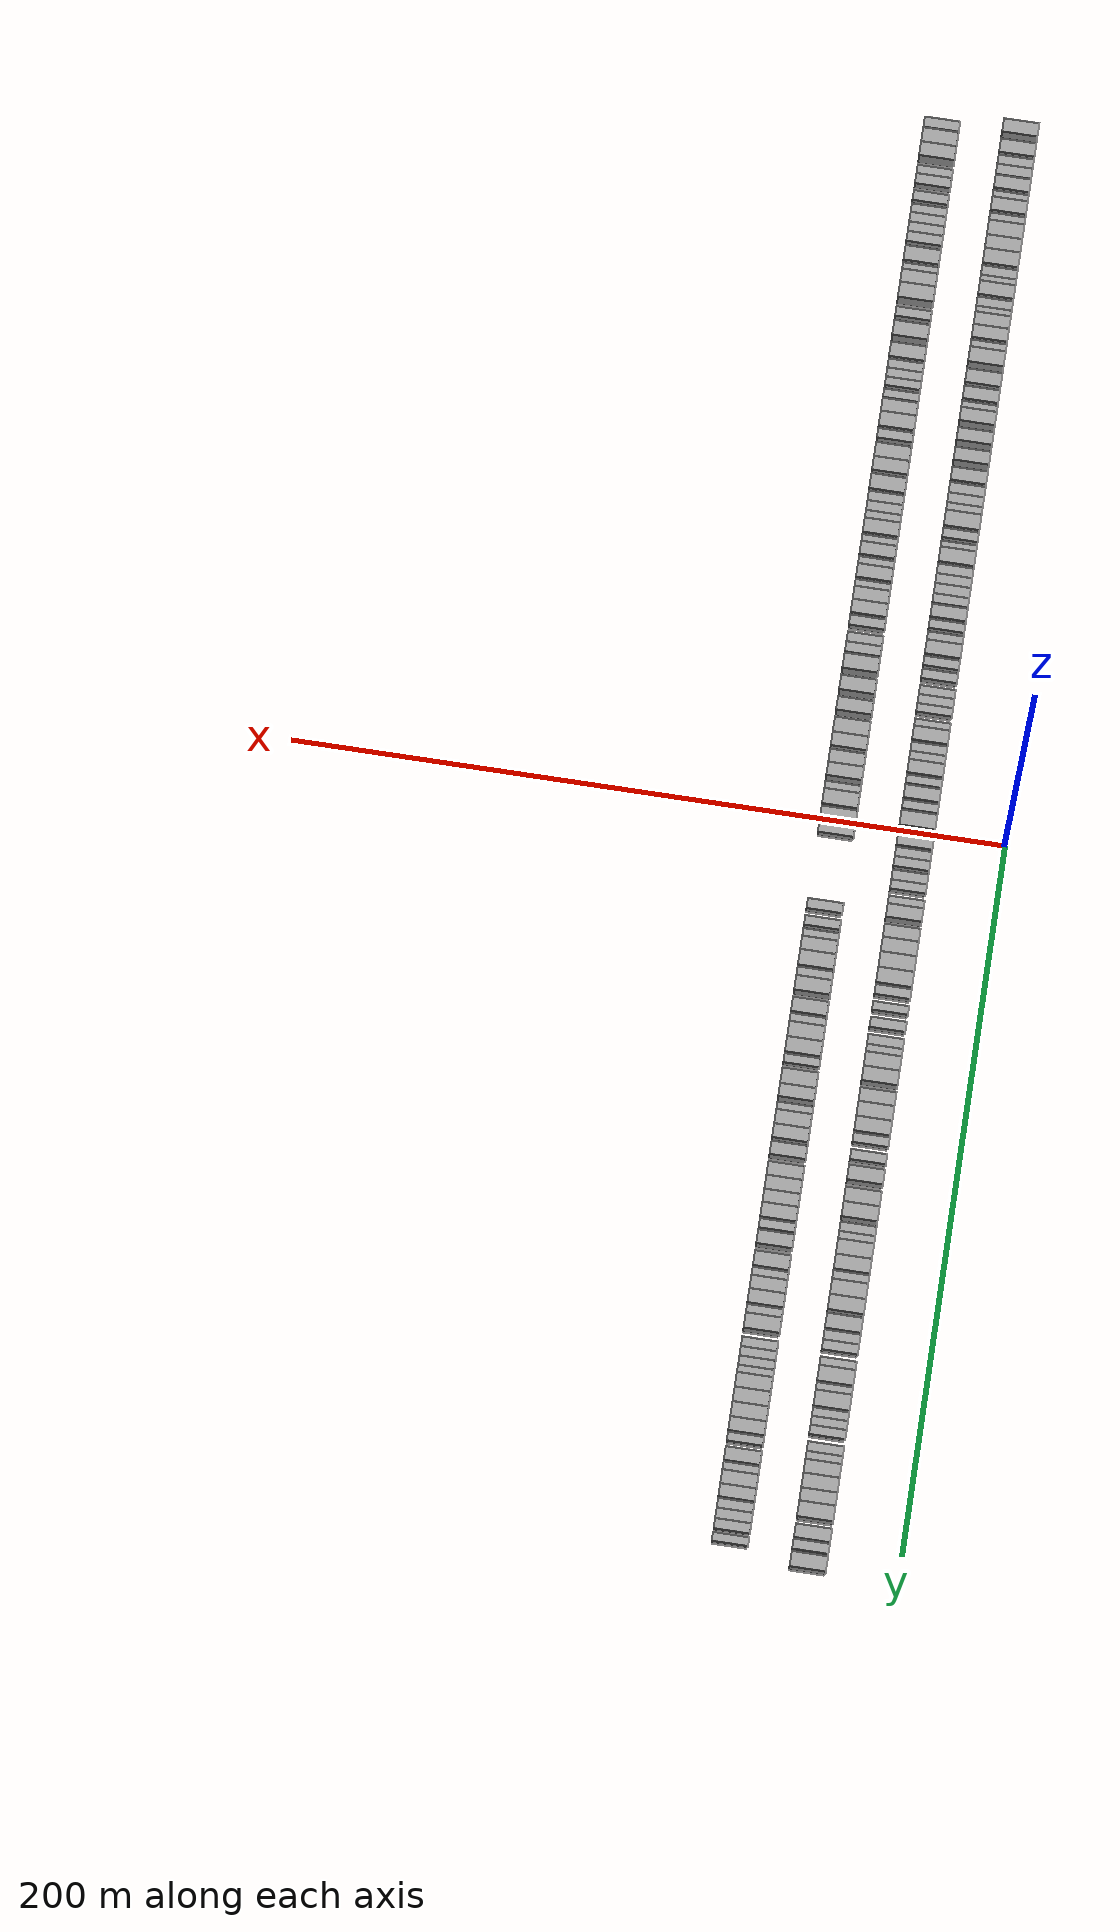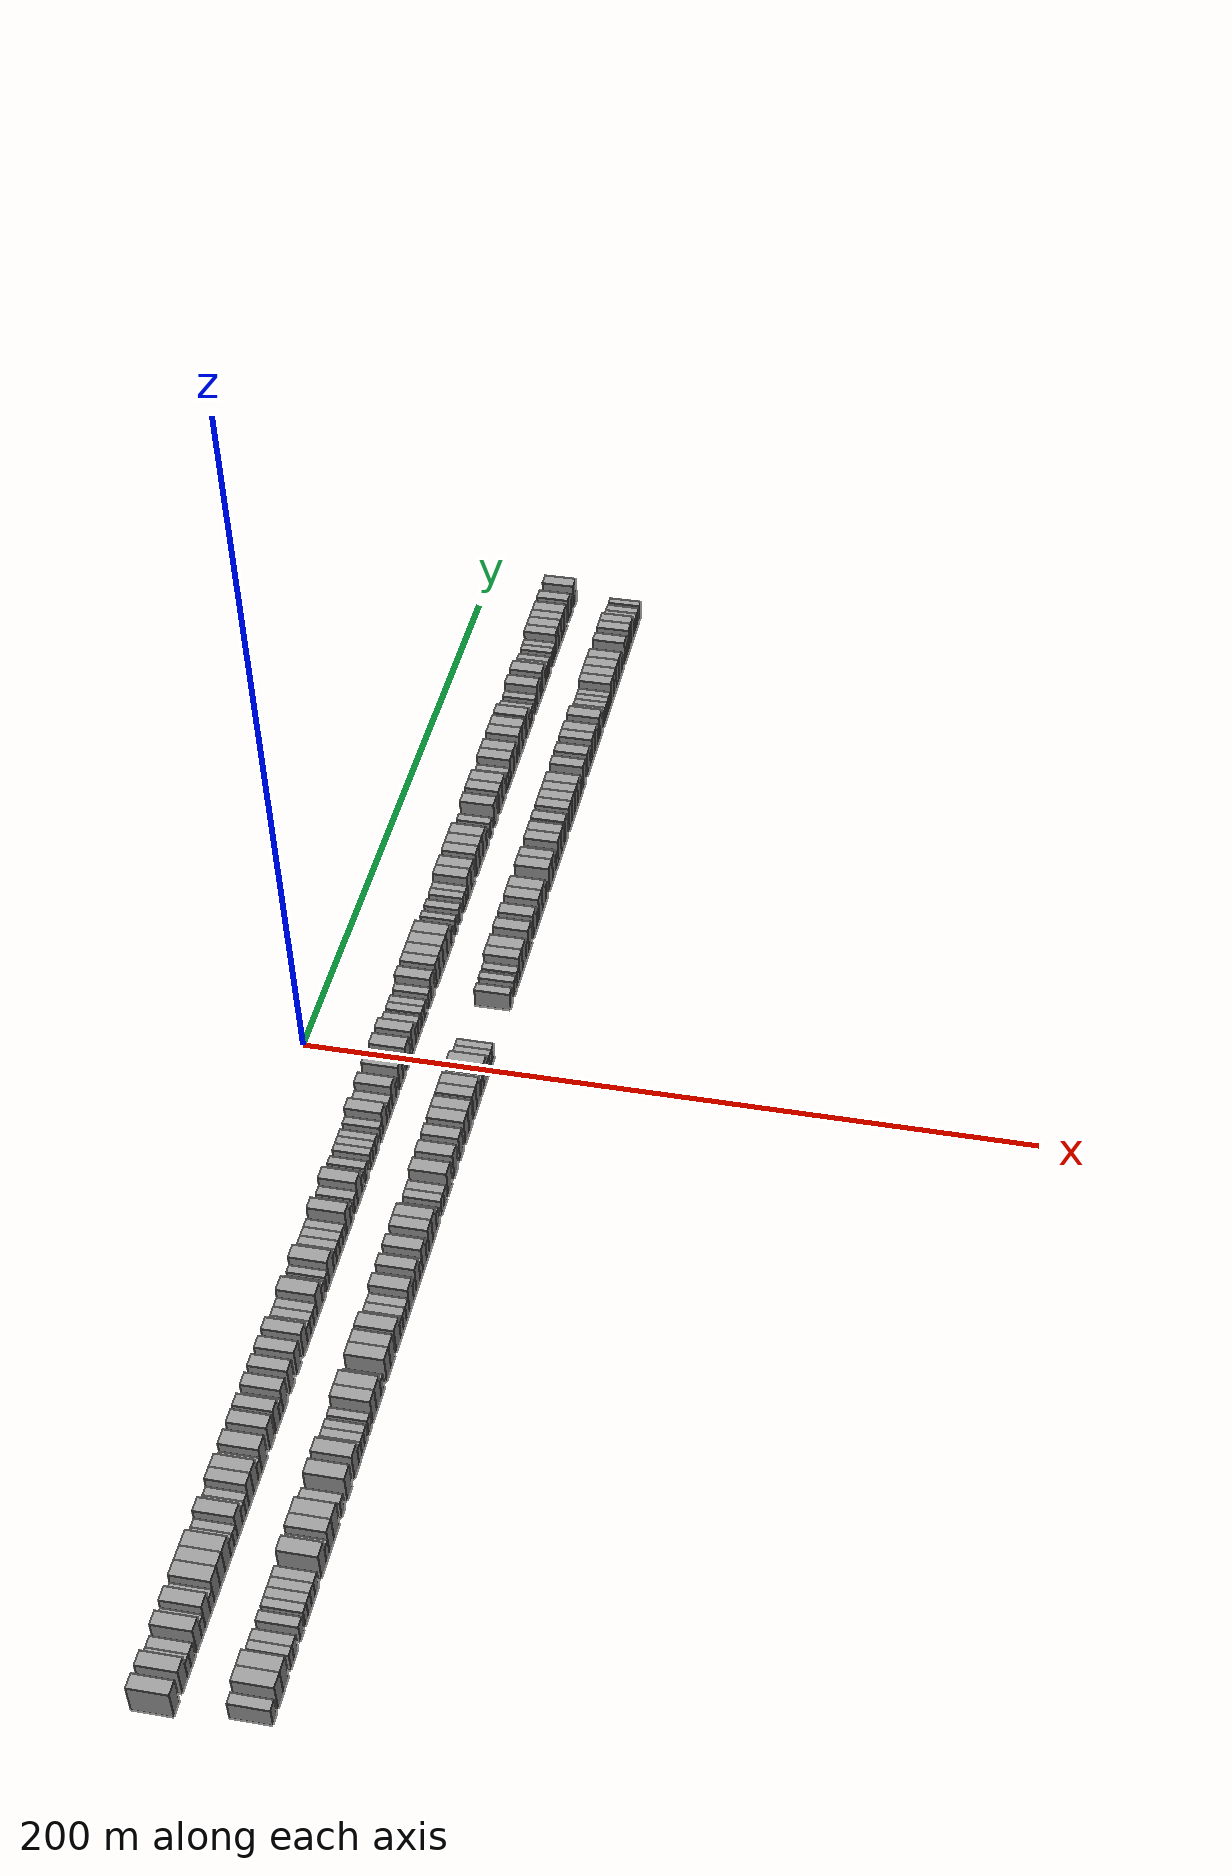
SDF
<sdf version="1.6">
 <world name="default">
  <scene>
   <sky><clouds><speed>12</speed></clouds></sky>
   <ambient>0.4 0.4 0.4 1</ambient>
   <background>0.7 0.7 0.7 1</background>
   <shadows>1</shadows>
  </scene>
  <gravity>0 0 -9.8066</gravity>
  <magnetic_field>6e-06 2.3e-05 -4.2e-05</magnetic_field>
  <physics default="0" name="default_physics" type="ode">
   <ode>
    <solver>
     <type>quick</type>
     <iters>10</iters>
     <sor>1.0</sor>
     <use_dynamic_moi_rescaling>0</use_dynamic_moi_rescaling>
    </solver>
    <constraints>
     <cfm>0</cfm>
     <erp>0.2</erp>
     <contact_max_correcting_vel>100</contact_max_correcting_vel>
     <contact_surface_layer>0.001</contact_surface_layer>
    </constraints>
   </ode>
   <max_step_size>0.004</max_step_size>
   <real_time_factor>1</real_time_factor>
   <real_time_update_rate>250</real_time_update_rate>
  </physics>
  <light name="sun" type="directional">
   <pose>0 0 10 0 0 0</pose>
   <diffuse>0.8 0.8 0.8 1</diffuse>
   <specular>0.2 0.2 0.2 1</specular>
   <attenuation>
    <range>1000</range>
    <constant>0.9</constant>
    <linear>0.01</linear>
    <quadratic>0.001</quadratic>
   </attenuation>
   <direction>-0.5 0.1 -0.9</direction>
  </light>
  <model name="building_1">
   <static>1</static>
   <pose>25.0000 -202.0652 0 0.000000 0.000000 0.000000</pose>
   <link name="link">
    <pose>0 0 4.50 0 0 0</pose>
    <collision name="collision"><geometry><box><size>10.0000 3.8695 9.0000</size></box></geometry></collision>
    <visual name="visual">
     <cast_shadows>0</cast_shadows>
     <geometry><box><size>10.0000 3.8695 9.0000</size></box></geometry>
     <material>
      <script>
       <uri>model://grey_wall/materials/scripts</uri>
       <uri>model://grey_wall/materials/textures</uri>
       <name>vrc/grey_wall</name>
      </script>
     </material>
    </visual>
   </link>
  </model>
  <model name="building_2">
   <static>1</static>
   <pose>25.0000 -196.1760 0 0.000000 0.000000 0.000000</pose>
   <link name="link">
    <pose>0 0 4.50 0 0 0</pose>
    <collision name="collision"><geometry><box><size>10.0000 3.9089 9.0000</size></box></geometry></collision>
    <visual name="visual">
     <cast_shadows>0</cast_shadows>
     <geometry><box><size>10.0000 3.9089 9.0000</size></box></geometry>
     <material>
      <script>
       <uri>model://grey_wall/materials/scripts</uri>
       <uri>model://grey_wall/materials/textures</uri>
       <name>vrc/grey_wall</name>
      </script>
     </material>
    </visual>
   </link>
  </model>
  <model name="building_3">
   <static>1</static>
   <pose>25.0000 -192.8934 0 0.000000 0.000000 0.000000</pose>
   <link name="link">
    <pose>0 0 3.00 0 0 0</pose>
    <collision name="collision"><geometry><box><size>10.0000 2.6564 6.0000</size></box></geometry></collision>
    <visual name="visual">
     <cast_shadows>0</cast_shadows>
     <geometry><box><size>10.0000 2.6564 6.0000</size></box></geometry>
     <material>
      <script>
       <uri>model://grey_wall/materials/scripts</uri>
       <uri>model://grey_wall/materials/textures</uri>
       <name>vrc/grey_wall</name>
      </script>
     </material>
    </visual>
   </link>
  </model>
  <model name="building_4">
   <static>1</static>
   <pose>25.0000 -190.0712 0 0.000000 0.000000 0.000000</pose>
   <link name="link">
    <pose>0 0 3.00 0 0 0</pose>
    <collision name="collision"><geometry><box><size>10.0000 2.9880 6.0000</size></box></geometry></collision>
    <visual name="visual">
     <cast_shadows>0</cast_shadows>
     <geometry><box><size>10.0000 2.9880 6.0000</size></box></geometry>
     <material>
      <script>
       <uri>model://grey_wall/materials/scripts</uri>
       <uri>model://grey_wall/materials/textures</uri>
       <name>vrc/grey_wall</name>
      </script>
     </material>
    </visual>
   </link>
  </model>
  <model name="building_5">
   <static>1</static>
   <pose>25.0000 -185.6982 0 0.000000 0.000000 0.000000</pose>
   <link name="link">
    <pose>0 0 4.50 0 0 0</pose>
    <collision name="collision"><geometry><box><size>10.0000 3.7579 9.0000</size></box></geometry></collision>
    <visual name="visual">
     <cast_shadows>0</cast_shadows>
     <geometry><box><size>10.0000 3.7579 9.0000</size></box></geometry>
     <material>
      <script>
       <uri>model://grey_wall/materials/scripts</uri>
       <uri>model://grey_wall/materials/textures</uri>
       <name>vrc/grey_wall</name>
      </script>
     </material>
    </visual>
   </link>
  </model>
  <model name="building_6">
   <static>1</static>
   <pose>25.0000 -182.5065 0 0.000000 0.000000 0.000000</pose>
   <link name="link">
    <pose>0 0 3.00 0 0 0</pose>
    <collision name="collision"><geometry><box><size>10.0000 2.6255 6.0000</size></box></geometry></collision>
    <visual name="visual">
     <cast_shadows>0</cast_shadows>
     <geometry><box><size>10.0000 2.6255 6.0000</size></box></geometry>
     <material>
      <script>
       <uri>model://grey_wall/materials/scripts</uri>
       <uri>model://grey_wall/materials/textures</uri>
       <name>vrc/grey_wall</name>
      </script>
     </material>
    </visual>
   </link>
  </model>
  <model name="building_7">
   <static>1</static>
   <pose>25.0000 -179.2586 0 0.000000 0.000000 0.000000</pose>
   <link name="link">
    <pose>0 0 4.50 0 0 0</pose>
    <collision name="collision"><geometry><box><size>10.0000 3.8704 9.0000</size></box></geometry></collision>
    <visual name="visual">
     <cast_shadows>0</cast_shadows>
     <geometry><box><size>10.0000 3.8704 9.0000</size></box></geometry>
     <material>
      <script>
       <uri>model://grey_wall/materials/scripts</uri>
       <uri>model://grey_wall/materials/textures</uri>
       <name>vrc/grey_wall</name>
      </script>
     </material>
    </visual>
   </link>
  </model>
  <model name="building_8">
   <static>1</static>
   <pose>25.0000 -175.8857 0 0.000000 0.000000 0.000000</pose>
   <link name="link">
    <pose>0 0 3.00 0 0 0</pose>
    <collision name="collision"><geometry><box><size>10.0000 2.8753 6.0000</size></box></geometry></collision>
    <visual name="visual">
     <cast_shadows>0</cast_shadows>
     <geometry><box><size>10.0000 2.8753 6.0000</size></box></geometry>
     <material>
      <script>
       <uri>model://grey_wall/materials/scripts</uri>
       <uri>model://grey_wall/materials/textures</uri>
       <name>vrc/grey_wall</name>
      </script>
     </material>
    </visual>
   </link>
  </model>
  <model name="building_9">
   <static>1</static>
   <pose>25.0000 -172.3090 0 0.000000 0.000000 0.000000</pose>
   <link name="link">
    <pose>0 0 4.50 0 0 0</pose>
    <collision name="collision"><geometry><box><size>10.0000 4.2781 9.0000</size></box></geometry></collision>
    <visual name="visual">
     <cast_shadows>0</cast_shadows>
     <geometry><box><size>10.0000 4.2781 9.0000</size></box></geometry>
     <material>
      <script>
       <uri>model://grey_wall/materials/scripts</uri>
       <uri>model://grey_wall/materials/textures</uri>
       <name>vrc/grey_wall</name>
      </script>
     </material>
    </visual>
   </link>
  </model>
  <model name="building_10">
   <static>1</static>
   <pose>25.0000 -168.2211 0 0.000000 0.000000 0.000000</pose>
   <link name="link">
    <pose>0 0 4.50 0 0 0</pose>
    <collision name="collision"><geometry><box><size>10.0000 3.8978 9.0000</size></box></geometry></collision>
    <visual name="visual">
     <cast_shadows>0</cast_shadows>
     <geometry><box><size>10.0000 3.8978 9.0000</size></box></geometry>
     <material>
      <script>
       <uri>model://grey_wall/materials/scripts</uri>
       <uri>model://grey_wall/materials/textures</uri>
       <name>vrc/grey_wall</name>
      </script>
     </material>
    </visual>
   </link>
  </model>
  <model name="building_11">
   <static>1</static>
   <pose>25.0000 -164.1070 0 0.000000 0.000000 0.000000</pose>
   <link name="link">
    <pose>0 0 4.50 0 0 0</pose>
    <collision name="collision"><geometry><box><size>10.0000 4.3304 9.0000</size></box></geometry></collision>
    <visual name="visual">
     <cast_shadows>0</cast_shadows>
     <geometry><box><size>10.0000 4.3304 9.0000</size></box></geometry>
     <material>
      <script>
       <uri>model://grey_wall/materials/scripts</uri>
       <uri>model://grey_wall/materials/textures</uri>
       <name>vrc/grey_wall</name>
      </script>
     </material>
    </visual>
   </link>
  </model>
  <model name="building_12">
   <static>1</static>
   <pose>25.0000 -160.5706 0 0.000000 0.000000 0.000000</pose>
   <link name="link">
    <pose>0 0 3.00 0 0 0</pose>
    <collision name="collision"><geometry><box><size>10.0000 2.7423 6.0000</size></box></geometry></collision>
    <visual name="visual">
     <cast_shadows>0</cast_shadows>
     <geometry><box><size>10.0000 2.7423 6.0000</size></box></geometry>
     <material>
      <script>
       <uri>model://grey_wall/materials/scripts</uri>
       <uri>model://grey_wall/materials/textures</uri>
       <name>vrc/grey_wall</name>
      </script>
     </material>
    </visual>
   </link>
  </model>
  <model name="building_13">
   <static>1</static>
   <pose>25.0000 -157.9767 0 0.000000 0.000000 0.000000</pose>
   <link name="link">
    <pose>0 0 3.00 0 0 0</pose>
    <collision name="collision"><geometry><box><size>10.0000 2.4453 6.0000</size></box></geometry></collision>
    <visual name="visual">
     <cast_shadows>0</cast_shadows>
     <geometry><box><size>10.0000 2.4453 6.0000</size></box></geometry>
     <material>
      <script>
       <uri>model://grey_wall/materials/scripts</uri>
       <uri>model://grey_wall/materials/textures</uri>
       <name>vrc/grey_wall</name>
      </script>
     </material>
    </visual>
   </link>
  </model>
  <model name="building_14">
   <static>1</static>
   <pose>25.0000 -154.7850 0 0.000000 0.000000 0.000000</pose>
   <link name="link">
    <pose>0 0 4.50 0 0 0</pose>
    <collision name="collision"><geometry><box><size>10.0000 3.9381 9.0000</size></box></geometry></collision>
    <visual name="visual">
     <cast_shadows>0</cast_shadows>
     <geometry><box><size>10.0000 3.9381 9.0000</size></box></geometry>
     <material>
      <script>
       <uri>model://grey_wall/materials/scripts</uri>
       <uri>model://grey_wall/materials/textures</uri>
       <name>vrc/grey_wall</name>
      </script>
     </material>
    </visual>
   </link>
  </model>
  <model name="building_15">
   <static>1</static>
   <pose>25.0000 -151.4833 0 0.000000 0.000000 0.000000</pose>
   <link name="link">
    <pose>0 0 3.00 0 0 0</pose>
    <collision name="collision"><geometry><box><size>10.0000 2.6653 6.0000</size></box></geometry></collision>
    <visual name="visual">
     <cast_shadows>0</cast_shadows>
     <geometry><box><size>10.0000 2.6653 6.0000</size></box></geometry>
     <material>
      <script>
       <uri>model://grey_wall/materials/scripts</uri>
       <uri>model://grey_wall/materials/textures</uri>
       <name>vrc/grey_wall</name>
      </script>
     </material>
    </visual>
   </link>
  </model>
  <model name="building_16">
   <static>1</static>
   <pose>25.0000 -148.9385 0 0.000000 0.000000 0.000000</pose>
   <link name="link">
    <pose>0 0 3.00 0 0 0</pose>
    <collision name="collision"><geometry><box><size>10.0000 2.4245 6.0000</size></box></geometry></collision>
    <visual name="visual">
     <cast_shadows>0</cast_shadows>
     <geometry><box><size>10.0000 2.4245 6.0000</size></box></geometry>
     <material>
      <script>
       <uri>model://grey_wall/materials/scripts</uri>
       <uri>model://grey_wall/materials/textures</uri>
       <name>vrc/grey_wall</name>
      </script>
     </material>
    </visual>
   </link>
  </model>
  <model name="building_17">
   <static>1</static>
   <pose>25.0000 -145.9141 0 0.000000 0.000000 0.000000</pose>
   <link name="link">
    <pose>0 0 4.50 0 0 0</pose>
    <collision name="collision"><geometry><box><size>10.0000 3.6242 9.0000</size></box></geometry></collision>
    <visual name="visual">
     <cast_shadows>0</cast_shadows>
     <geometry><box><size>10.0000 3.6242 9.0000</size></box></geometry>
     <material>
      <script>
       <uri>model://grey_wall/materials/scripts</uri>
       <uri>model://grey_wall/materials/textures</uri>
       <name>vrc/grey_wall</name>
      </script>
     </material>
    </visual>
   </link>
  </model>
  <model name="building_18">
   <static>1</static>
   <pose>25.0000 -142.2166 0 0.000000 0.000000 0.000000</pose>
   <link name="link">
    <pose>0 0 4.50 0 0 0</pose>
    <collision name="collision"><geometry><box><size>10.0000 3.7708 9.0000</size></box></geometry></collision>
    <visual name="visual">
     <cast_shadows>0</cast_shadows>
     <geometry><box><size>10.0000 3.7708 9.0000</size></box></geometry>
     <material>
      <script>
       <uri>model://grey_wall/materials/scripts</uri>
       <uri>model://grey_wall/materials/textures</uri>
       <name>vrc/grey_wall</name>
      </script>
     </material>
    </visual>
   </link>
  </model>
  <model name="building_19">
   <static>1</static>
   <pose>25.0000 -138.9541 0 0.000000 0.000000 0.000000</pose>
   <link name="link">
    <pose>0 0 3.00 0 0 0</pose>
    <collision name="collision"><geometry><box><size>10.0000 2.7542 6.0000</size></box></geometry></collision>
    <visual name="visual">
     <cast_shadows>0</cast_shadows>
     <geometry><box><size>10.0000 2.7542 6.0000</size></box></geometry>
     <material>
      <script>
       <uri>model://grey_wall/materials/scripts</uri>
       <uri>model://grey_wall/materials/textures</uri>
       <name>vrc/grey_wall</name>
      </script>
     </material>
    </visual>
   </link>
  </model>
  <model name="building_20">
   <static>1</static>
   <pose>25.0000 -135.4102 0 0.000000 0.000000 0.000000</pose>
   <link name="link">
    <pose>0 0 4.50 0 0 0</pose>
    <collision name="collision"><geometry><box><size>10.0000 4.3336 9.0000</size></box></geometry></collision>
    <visual name="visual">
     <cast_shadows>0</cast_shadows>
     <geometry><box><size>10.0000 4.3336 9.0000</size></box></geometry>
     <material>
      <script>
       <uri>model://grey_wall/materials/scripts</uri>
       <uri>model://grey_wall/materials/textures</uri>
       <name>vrc/grey_wall</name>
      </script>
     </material>
    </visual>
   </link>
  </model>
  <model name="building_21">
   <static>1</static>
   <pose>25.0000 -129.2474 0 0.000000 0.000000 0.000000</pose>
   <link name="link">
    <pose>0 0 4.50 0 0 0</pose>
    <collision name="collision"><geometry><box><size>10.0000 3.9918 9.0000</size></box></geometry></collision>
    <visual name="visual">
     <cast_shadows>0</cast_shadows>
     <geometry><box><size>10.0000 3.9918 9.0000</size></box></geometry>
     <material>
      <script>
       <uri>model://grey_wall/materials/scripts</uri>
       <uri>model://grey_wall/materials/textures</uri>
       <name>vrc/grey_wall</name>
      </script>
     </material>
    </visual>
   </link>
  </model>
  <model name="building_22">
   <static>1</static>
   <pose>25.0000 -124.4086 0 0.000000 0.000000 0.000000</pose>
   <link name="link">
    <pose>0 0 4.50 0 0 0</pose>
    <collision name="collision"><geometry><box><size>10.0000 3.6859 9.0000</size></box></geometry></collision>
    <visual name="visual">
     <cast_shadows>0</cast_shadows>
     <geometry><box><size>10.0000 3.6859 9.0000</size></box></geometry>
     <material>
      <script>
       <uri>model://grey_wall/materials/scripts</uri>
       <uri>model://grey_wall/materials/textures</uri>
       <name>vrc/grey_wall</name>
      </script>
     </material>
    </visual>
   </link>
  </model>
  <model name="building_23">
   <static>1</static>
   <pose>25.0000 -121.2948 0 0.000000 0.000000 0.000000</pose>
   <link name="link">
    <pose>0 0 3.00 0 0 0</pose>
    <collision name="collision"><geometry><box><size>10.0000 2.5416 6.0000</size></box></geometry></collision>
    <visual name="visual">
     <cast_shadows>0</cast_shadows>
     <geometry><box><size>10.0000 2.5416 6.0000</size></box></geometry>
     <material>
      <script>
       <uri>model://grey_wall/materials/scripts</uri>
       <uri>model://grey_wall/materials/textures</uri>
       <name>vrc/grey_wall</name>
      </script>
     </material>
    </visual>
   </link>
  </model>
  <model name="building_24">
   <static>1</static>
   <pose>25.0000 -118.1047 0 0.000000 0.000000 0.000000</pose>
   <link name="link">
    <pose>0 0 4.50 0 0 0</pose>
    <collision name="collision"><geometry><box><size>10.0000 3.8387 9.0000</size></box></geometry></collision>
    <visual name="visual">
     <cast_shadows>0</cast_shadows>
     <geometry><box><size>10.0000 3.8387 9.0000</size></box></geometry>
     <material>
      <script>
       <uri>model://grey_wall/materials/scripts</uri>
       <uri>model://grey_wall/materials/textures</uri>
       <name>vrc/grey_wall</name>
      </script>
     </material>
    </visual>
   </link>
  </model>
  <model name="building_25">
   <static>1</static>
   <pose>25.0000 -112.3611 0 0.000000 0.000000 0.000000</pose>
   <link name="link">
    <pose>0 0 4.50 0 0 0</pose>
    <collision name="collision"><geometry><box><size>10.0000 3.6486 9.0000</size></box></geometry></collision>
    <visual name="visual">
     <cast_shadows>0</cast_shadows>
     <geometry><box><size>10.0000 3.6486 9.0000</size></box></geometry>
     <material>
      <script>
       <uri>model://grey_wall/materials/scripts</uri>
       <uri>model://grey_wall/materials/textures</uri>
       <name>vrc/grey_wall</name>
      </script>
     </material>
    </visual>
   </link>
  </model>
  <model name="building_26">
   <static>1</static>
   <pose>25.0000 -106.6655 0 0.000000 0.000000 0.000000</pose>
   <link name="link">
    <pose>0 0 4.50 0 0 0</pose>
    <collision name="collision"><geometry><box><size>10.0000 3.7426 9.0000</size></box></geometry></collision>
    <visual name="visual">
     <cast_shadows>0</cast_shadows>
     <geometry><box><size>10.0000 3.7426 9.0000</size></box></geometry>
     <material>
      <script>
       <uri>model://grey_wall/materials/scripts</uri>
       <uri>model://grey_wall/materials/textures</uri>
       <name>vrc/grey_wall</name>
      </script>
     </material>
    </visual>
   </link>
  </model>
  <model name="building_27">
   <static>1</static>
   <pose>25.0000 -100.9194 0 0.000000 0.000000 0.000000</pose>
   <link name="link">
    <pose>0 0 4.50 0 0 0</pose>
    <collision name="collision"><geometry><box><size>10.0000 3.7495 9.0000</size></box></geometry></collision>
    <visual name="visual">
     <cast_shadows>0</cast_shadows>
     <geometry><box><size>10.0000 3.7495 9.0000</size></box></geometry>
     <material>
      <script>
       <uri>model://grey_wall/materials/scripts</uri>
       <uri>model://grey_wall/materials/textures</uri>
       <name>vrc/grey_wall</name>
      </script>
     </material>
    </visual>
   </link>
  </model>
  <model name="building_28">
   <static>1</static>
   <pose>25.0000 -97.5588 0 0.000000 0.000000 0.000000</pose>
   <link name="link">
    <pose>0 0 3.00 0 0 0</pose>
    <collision name="collision"><geometry><box><size>10.0000 2.9717 6.0000</size></box></geometry></collision>
    <visual name="visual">
     <cast_shadows>0</cast_shadows>
     <geometry><box><size>10.0000 2.9717 6.0000</size></box></geometry>
     <material>
      <script>
       <uri>model://grey_wall/materials/scripts</uri>
       <uri>model://grey_wall/materials/textures</uri>
       <name>vrc/grey_wall</name>
      </script>
     </material>
    </visual>
   </link>
  </model>
  <model name="building_29">
   <static>1</static>
   <pose>25.0000 -94.6453 0 0.000000 0.000000 0.000000</pose>
   <link name="link">
    <pose>0 0 3.00 0 0 0</pose>
    <collision name="collision"><geometry><box><size>10.0000 2.8553 6.0000</size></box></geometry></collision>
    <visual name="visual">
     <cast_shadows>0</cast_shadows>
     <geometry><box><size>10.0000 2.8553 6.0000</size></box></geometry>
     <material>
      <script>
       <uri>model://grey_wall/materials/scripts</uri>
       <uri>model://grey_wall/materials/textures</uri>
       <name>vrc/grey_wall</name>
      </script>
     </material>
    </visual>
   </link>
  </model>
  <model name="building_30">
   <static>1</static>
   <pose>25.0000 -91.7965 0 0.000000 0.000000 0.000000</pose>
   <link name="link">
    <pose>0 0 3.00 0 0 0</pose>
    <collision name="collision"><geometry><box><size>10.0000 2.8423 6.0000</size></box></geometry></collision>
    <visual name="visual">
     <cast_shadows>0</cast_shadows>
     <geometry><box><size>10.0000 2.8423 6.0000</size></box></geometry>
     <material>
      <script>
       <uri>model://grey_wall/materials/scripts</uri>
       <uri>model://grey_wall/materials/textures</uri>
       <name>vrc/grey_wall</name>
      </script>
     </material>
    </visual>
   </link>
  </model>
  <model name="building_31">
   <static>1</static>
   <pose>25.0000 -88.1324 0 0.000000 0.000000 0.000000</pose>
   <link name="link">
    <pose>0 0 4.50 0 0 0</pose>
    <collision name="collision"><geometry><box><size>10.0000 4.4860 9.0000</size></box></geometry></collision>
    <visual name="visual">
     <cast_shadows>0</cast_shadows>
     <geometry><box><size>10.0000 4.4860 9.0000</size></box></geometry>
     <material>
      <script>
       <uri>model://grey_wall/materials/scripts</uri>
       <uri>model://grey_wall/materials/textures</uri>
       <name>vrc/grey_wall</name>
      </script>
     </material>
    </visual>
   </link>
  </model>
  <model name="building_32">
   <static>1</static>
   <pose>25.0000 -84.5244 0 0.000000 0.000000 0.000000</pose>
   <link name="link">
    <pose>0 0 3.00 0 0 0</pose>
    <collision name="collision"><geometry><box><size>10.0000 2.7300 6.0000</size></box></geometry></collision>
    <visual name="visual">
     <cast_shadows>0</cast_shadows>
     <geometry><box><size>10.0000 2.7300 6.0000</size></box></geometry>
     <material>
      <script>
       <uri>model://grey_wall/materials/scripts</uri>
       <uri>model://grey_wall/materials/textures</uri>
       <name>vrc/grey_wall</name>
      </script>
     </material>
    </visual>
   </link>
  </model>
  <model name="building_33">
   <static>1</static>
   <pose>25.0000 -80.9583 0 0.000000 0.000000 0.000000</pose>
   <link name="link">
    <pose>0 0 3.00 0 0 0</pose>
    <collision name="collision"><geometry><box><size>10.0000 2.4023 6.0000</size></box></geometry></collision>
    <visual name="visual">
     <cast_shadows>0</cast_shadows>
     <geometry><box><size>10.0000 2.4023 6.0000</size></box></geometry>
     <material>
      <script>
       <uri>model://grey_wall/materials/scripts</uri>
       <uri>model://grey_wall/materials/textures</uri>
       <name>vrc/grey_wall</name>
      </script>
     </material>
    </visual>
   </link>
  </model>
  <model name="building_34">
   <static>1</static>
   <pose>25.0000 -77.6460 0 0.000000 0.000000 0.000000</pose>
   <link name="link">
    <pose>0 0 4.50 0 0 0</pose>
    <collision name="collision"><geometry><box><size>10.0000 4.2224 9.0000</size></box></geometry></collision>
    <visual name="visual">
     <cast_shadows>0</cast_shadows>
     <geometry><box><size>10.0000 4.2224 9.0000</size></box></geometry>
     <material>
      <script>
       <uri>model://grey_wall/materials/scripts</uri>
       <uri>model://grey_wall/materials/textures</uri>
       <name>vrc/grey_wall</name>
      </script>
     </material>
    </visual>
   </link>
  </model>
  <model name="building_35">
   <static>1</static>
   <pose>25.0000 -74.1463 0 0.000000 0.000000 0.000000</pose>
   <link name="link">
    <pose>0 0 3.00 0 0 0</pose>
    <collision name="collision"><geometry><box><size>10.0000 2.7769 6.0000</size></box></geometry></collision>
    <visual name="visual">
     <cast_shadows>0</cast_shadows>
     <geometry><box><size>10.0000 2.7769 6.0000</size></box></geometry>
     <material>
      <script>
       <uri>model://grey_wall/materials/scripts</uri>
       <uri>model://grey_wall/materials/textures</uri>
       <name>vrc/grey_wall</name>
      </script>
     </material>
    </visual>
   </link>
  </model>
  <model name="building_36">
   <static>1</static>
   <pose>25.0000 -71.3508 0 0.000000 0.000000 0.000000</pose>
   <link name="link">
    <pose>0 0 3.00 0 0 0</pose>
    <collision name="collision"><geometry><box><size>10.0000 2.8141 6.0000</size></box></geometry></collision>
    <visual name="visual">
     <cast_shadows>0</cast_shadows>
     <geometry><box><size>10.0000 2.8141 6.0000</size></box></geometry>
     <material>
      <script>
       <uri>model://grey_wall/materials/scripts</uri>
       <uri>model://grey_wall/materials/textures</uri>
       <name>vrc/grey_wall</name>
      </script>
     </material>
    </visual>
   </link>
  </model>
  <model name="building_37">
   <static>1</static>
   <pose>25.0000 -68.4690 0 0.000000 0.000000 0.000000</pose>
   <link name="link">
    <pose>0 0 3.00 0 0 0</pose>
    <collision name="collision"><geometry><box><size>10.0000 2.9496 6.0000</size></box></geometry></collision>
    <visual name="visual">
     <cast_shadows>0</cast_shadows>
     <geometry><box><size>10.0000 2.9496 6.0000</size></box></geometry>
     <material>
      <script>
       <uri>model://grey_wall/materials/scripts</uri>
       <uri>model://grey_wall/materials/textures</uri>
       <name>vrc/grey_wall</name>
      </script>
     </material>
    </visual>
   </link>
  </model>
  <model name="building_38">
   <static>1</static>
   <pose>25.0000 -65.6569 0 0.000000 0.000000 0.000000</pose>
   <link name="link">
    <pose>0 0 3.00 0 0 0</pose>
    <collision name="collision"><geometry><box><size>10.0000 2.6744 6.0000</size></box></geometry></collision>
    <visual name="visual">
     <cast_shadows>0</cast_shadows>
     <geometry><box><size>10.0000 2.6744 6.0000</size></box></geometry>
     <material>
      <script>
       <uri>model://grey_wall/materials/scripts</uri>
       <uri>model://grey_wall/materials/textures</uri>
       <name>vrc/grey_wall</name>
      </script>
     </material>
    </visual>
   </link>
  </model>
  <model name="building_39">
   <static>1</static>
   <pose>25.0000 -61.4845 0 0.000000 0.000000 0.000000</pose>
   <link name="link">
    <pose>0 0 4.50 0 0 0</pose>
    <collision name="collision"><geometry><box><size>10.0000 3.6704 9.0000</size></box></geometry></collision>
    <visual name="visual">
     <cast_shadows>0</cast_shadows>
     <geometry><box><size>10.0000 3.6704 9.0000</size></box></geometry>
     <material>
      <script>
       <uri>model://grey_wall/materials/scripts</uri>
       <uri>model://grey_wall/materials/textures</uri>
       <name>vrc/grey_wall</name>
      </script>
     </material>
    </visual>
   </link>
  </model>
  <model name="building_40">
   <static>1</static>
   <pose>25.0000 -58.3375 0 0.000000 0.000000 0.000000</pose>
   <link name="link">
    <pose>0 0 3.00 0 0 0</pose>
    <collision name="collision"><geometry><box><size>10.0000 2.6237 6.0000</size></box></geometry></collision>
    <visual name="visual">
     <cast_shadows>0</cast_shadows>
     <geometry><box><size>10.0000 2.6237 6.0000</size></box></geometry>
     <material>
      <script>
       <uri>model://grey_wall/materials/scripts</uri>
       <uri>model://grey_wall/materials/textures</uri>
       <name>vrc/grey_wall</name>
      </script>
     </material>
    </visual>
   </link>
  </model>
  <model name="building_41">
   <static>1</static>
   <pose>25.0000 -54.5407 0 0.000000 0.000000 0.000000</pose>
   <link name="link">
    <pose>0 0 3.00 0 0 0</pose>
    <collision name="collision"><geometry><box><size>10.0000 2.9699 6.0000</size></box></geometry></collision>
    <visual name="visual">
     <cast_shadows>0</cast_shadows>
     <geometry><box><size>10.0000 2.9699 6.0000</size></box></geometry>
     <material>
      <script>
       <uri>model://grey_wall/materials/scripts</uri>
       <uri>model://grey_wall/materials/textures</uri>
       <name>vrc/grey_wall</name>
      </script>
     </material>
    </visual>
   </link>
  </model>
  <model name="building_42">
   <static>1</static>
   <pose>25.0000 -51.0551 0 0.000000 0.000000 0.000000</pose>
   <link name="link">
    <pose>0 0 4.50 0 0 0</pose>
    <collision name="collision"><geometry><box><size>10.0000 4.0013 9.0000</size></box></geometry></collision>
    <visual name="visual">
     <cast_shadows>0</cast_shadows>
     <geometry><box><size>10.0000 4.0013 9.0000</size></box></geometry>
     <material>
      <script>
       <uri>model://grey_wall/materials/scripts</uri>
       <uri>model://grey_wall/materials/textures</uri>
       <name>vrc/grey_wall</name>
      </script>
     </material>
    </visual>
   </link>
  </model>
  <model name="building_43">
   <static>1</static>
   <pose>25.0000 -47.6975 0 0.000000 0.000000 0.000000</pose>
   <link name="link">
    <pose>0 0 3.00 0 0 0</pose>
    <collision name="collision"><geometry><box><size>10.0000 2.7139 6.0000</size></box></geometry></collision>
    <visual name="visual">
     <cast_shadows>0</cast_shadows>
     <geometry><box><size>10.0000 2.7139 6.0000</size></box></geometry>
     <material>
      <script>
       <uri>model://grey_wall/materials/scripts</uri>
       <uri>model://grey_wall/materials/textures</uri>
       <name>vrc/grey_wall</name>
      </script>
     </material>
    </visual>
   </link>
  </model>
  <model name="building_44">
   <static>1</static>
   <pose>25.0000 -43.9743 0 0.000000 0.000000 0.000000</pose>
   <link name="link">
    <pose>0 0 3.00 0 0 0</pose>
    <collision name="collision"><geometry><box><size>10.0000 2.7326 6.0000</size></box></geometry></collision>
    <visual name="visual">
     <cast_shadows>0</cast_shadows>
     <geometry><box><size>10.0000 2.7326 6.0000</size></box></geometry>
     <material>
      <script>
       <uri>model://grey_wall/materials/scripts</uri>
       <uri>model://grey_wall/materials/textures</uri>
       <name>vrc/grey_wall</name>
      </script>
     </material>
    </visual>
   </link>
  </model>
  <model name="building_45">
   <static>1</static>
   <pose>25.0000 -39.3342 0 0.000000 0.000000 0.000000</pose>
   <link name="link">
    <pose>0 0 3.00 0 0 0</pose>
    <collision name="collision"><geometry><box><size>10.0000 2.5474 6.0000</size></box></geometry></collision>
    <visual name="visual">
     <cast_shadows>0</cast_shadows>
     <geometry><box><size>10.0000 2.5474 6.0000</size></box></geometry>
     <material>
      <script>
       <uri>model://grey_wall/materials/scripts</uri>
       <uri>model://grey_wall/materials/textures</uri>
       <name>vrc/grey_wall</name>
      </script>
     </material>
    </visual>
   </link>
  </model>
  <model name="building_46">
   <static>1</static>
   <pose>25.0000 -36.7564 0 0.000000 0.000000 0.000000</pose>
   <link name="link">
    <pose>0 0 3.00 0 0 0</pose>
    <collision name="collision"><geometry><box><size>10.0000 2.6083 6.0000</size></box></geometry></collision>
    <visual name="visual">
     <cast_shadows>0</cast_shadows>
     <geometry><box><size>10.0000 2.6083 6.0000</size></box></geometry>
     <material>
      <script>
       <uri>model://grey_wall/materials/scripts</uri>
       <uri>model://grey_wall/materials/textures</uri>
       <name>vrc/grey_wall</name>
      </script>
     </material>
    </visual>
   </link>
  </model>
  <model name="building_47">
   <static>1</static>
   <pose>25.0000 -34.2392 0 0.000000 0.000000 0.000000</pose>
   <link name="link">
    <pose>0 0 3.00 0 0 0</pose>
    <collision name="collision"><geometry><box><size>10.0000 2.4261 6.0000</size></box></geometry></collision>
    <visual name="visual">
     <cast_shadows>0</cast_shadows>
     <geometry><box><size>10.0000 2.4261 6.0000</size></box></geometry>
     <material>
      <script>
       <uri>model://grey_wall/materials/scripts</uri>
       <uri>model://grey_wall/materials/textures</uri>
       <name>vrc/grey_wall</name>
      </script>
     </material>
    </visual>
   </link>
  </model>
  <model name="building_48">
   <static>1</static>
   <pose>25.0000 -29.7129 0 0.000000 0.000000 0.000000</pose>
   <link name="link">
    <pose>0 0 3.00 0 0 0</pose>
    <collision name="collision"><geometry><box><size>10.0000 2.6264 6.0000</size></box></geometry></collision>
    <visual name="visual">
     <cast_shadows>0</cast_shadows>
     <geometry><box><size>10.0000 2.6264 6.0000</size></box></geometry>
     <material>
      <script>
       <uri>model://grey_wall/materials/scripts</uri>
       <uri>model://grey_wall/materials/textures</uri>
       <name>vrc/grey_wall</name>
      </script>
     </material>
    </visual>
   </link>
  </model>
  <model name="building_49">
   <static>1</static>
   <pose>25.0000 -26.4255 0 0.000000 0.000000 0.000000</pose>
   <link name="link">
    <pose>0 0 4.50 0 0 0</pose>
    <collision name="collision"><geometry><box><size>10.0000 3.9484 9.0000</size></box></geometry></collision>
    <visual name="visual">
     <cast_shadows>0</cast_shadows>
     <geometry><box><size>10.0000 3.9484 9.0000</size></box></geometry>
     <material>
      <script>
       <uri>model://grey_wall/materials/scripts</uri>
       <uri>model://grey_wall/materials/textures</uri>
       <name>vrc/grey_wall</name>
      </script>
     </material>
    </visual>
   </link>
  </model>
  <model name="building_50">
   <static>1</static>
   <pose>25.0000 -23.1277 0 0.000000 0.000000 0.000000</pose>
   <link name="link">
    <pose>0 0 3.00 0 0 0</pose>
    <collision name="collision"><geometry><box><size>10.0000 2.6472 6.0000</size></box></geometry></collision>
    <visual name="visual">
     <cast_shadows>0</cast_shadows>
     <geometry><box><size>10.0000 2.6472 6.0000</size></box></geometry>
     <material>
      <script>
       <uri>model://grey_wall/materials/scripts</uri>
       <uri>model://grey_wall/materials/textures</uri>
       <name>vrc/grey_wall</name>
      </script>
     </material>
    </visual>
   </link>
  </model>
  <model name="building_51">
   <static>1</static>
   <pose>25.0000 -20.3226 0 0.000000 0.000000 0.000000</pose>
   <link name="link">
    <pose>0 0 3.00 0 0 0</pose>
    <collision name="collision"><geometry><box><size>10.0000 2.9630 6.0000</size></box></geometry></collision>
    <visual name="visual">
     <cast_shadows>0</cast_shadows>
     <geometry><box><size>10.0000 2.9630 6.0000</size></box></geometry>
     <material>
      <script>
       <uri>model://grey_wall/materials/scripts</uri>
       <uri>model://grey_wall/materials/textures</uri>
       <name>vrc/grey_wall</name>
      </script>
     </material>
    </visual>
   </link>
  </model>
  <model name="building_52">
   <static>1</static>
   <pose>25.0000 -16.9507 0 0.000000 0.000000 0.000000</pose>
   <link name="link">
    <pose>0 0 4.50 0 0 0</pose>
    <collision name="collision"><geometry><box><size>10.0000 3.7808 9.0000</size></box></geometry></collision>
    <visual name="visual">
     <cast_shadows>0</cast_shadows>
     <geometry><box><size>10.0000 3.7808 9.0000</size></box></geometry>
     <material>
      <script>
       <uri>model://grey_wall/materials/scripts</uri>
       <uri>model://grey_wall/materials/textures</uri>
       <name>vrc/grey_wall</name>
      </script>
     </material>
    </visual>
   </link>
  </model>
  <model name="building_53">
   <static>1</static>
   <pose>25.0000 -13.8546 0 0.000000 0.000000 0.000000</pose>
   <link name="link">
    <pose>0 0 3.00 0 0 0</pose>
    <collision name="collision"><geometry><box><size>10.0000 2.4114 6.0000</size></box></geometry></collision>
    <visual name="visual">
     <cast_shadows>0</cast_shadows>
     <geometry><box><size>10.0000 2.4114 6.0000</size></box></geometry>
     <material>
      <script>
       <uri>model://grey_wall/materials/scripts</uri>
       <uri>model://grey_wall/materials/textures</uri>
       <name>vrc/grey_wall</name>
      </script>
     </material>
    </visual>
   </link>
  </model>
  <model name="building_54">
   <static>1</static>
   <pose>25.0000 -9.7814 0 0.000000 0.000000 0.000000</pose>
   <link name="link">
    <pose>0 0 4.50 0 0 0</pose>
    <collision name="collision"><geometry><box><size>10.0000 3.7350 9.0000</size></box></geometry></collision>
    <visual name="visual">
     <cast_shadows>0</cast_shadows>
     <geometry><box><size>10.0000 3.7350 9.0000</size></box></geometry>
     <material>
      <script>
       <uri>model://grey_wall/materials/scripts</uri>
       <uri>model://grey_wall/materials/textures</uri>
       <name>vrc/grey_wall</name>
      </script>
     </material>
    </visual>
   </link>
  </model>
  <model name="building_55">
   <static>1</static>
   <pose>25.0000 -6.6591 0 0.000000 0.000000 0.000000</pose>
   <link name="link">
    <pose>0 0 3.00 0 0 0</pose>
    <collision name="collision"><geometry><box><size>10.0000 2.5096 6.0000</size></box></geometry></collision>
    <visual name="visual">
     <cast_shadows>0</cast_shadows>
     <geometry><box><size>10.0000 2.5096 6.0000</size></box></geometry>
     <material>
      <script>
       <uri>model://grey_wall/materials/scripts</uri>
       <uri>model://grey_wall/materials/textures</uri>
       <name>vrc/grey_wall</name>
      </script>
     </material>
    </visual>
   </link>
  </model>
  <model name="building_56">
   <static>1</static>
   <pose>25.0000 -2.2731 0 0.000000 0.000000 0.000000</pose>
   <link name="link">
    <pose>0 0 4.50 0 0 0</pose>
    <collision name="collision"><geometry><box><size>10.0000 4.2625 9.0000</size></box></geometry></collision>
    <visual name="visual">
     <cast_shadows>0</cast_shadows>
     <geometry><box><size>10.0000 4.2625 9.0000</size></box></geometry>
     <material>
      <script>
       <uri>model://grey_wall/materials/scripts</uri>
       <uri>model://grey_wall/materials/textures</uri>
       <name>vrc/grey_wall</name>
      </script>
     </material>
    </visual>
   </link>
  </model>
  <model name="building_57">
   <static>1</static>
   <pose>25.0000 3.7232 0 0.000000 0.000000 0.000000</pose>
   <link name="link">
    <pose>0 0 4.50 0 0 0</pose>
    <collision name="collision"><geometry><box><size>10.0000 3.7302 9.0000</size></box></geometry></collision>
    <visual name="visual">
     <cast_shadows>0</cast_shadows>
     <geometry><box><size>10.0000 3.7302 9.0000</size></box></geometry>
     <material>
      <script>
       <uri>model://grey_wall/materials/scripts</uri>
       <uri>model://grey_wall/materials/textures</uri>
       <name>vrc/grey_wall</name>
      </script>
     </material>
    </visual>
   </link>
  </model>
  <model name="building_58">
   <static>1</static>
   <pose>25.0000 6.9071 0 0.000000 0.000000 0.000000</pose>
   <link name="link">
    <pose>0 0 3.00 0 0 0</pose>
    <collision name="collision"><geometry><box><size>10.0000 2.6374 6.0000</size></box></geometry></collision>
    <visual name="visual">
     <cast_shadows>0</cast_shadows>
     <geometry><box><size>10.0000 2.6374 6.0000</size></box></geometry>
     <material>
      <script>
       <uri>model://grey_wall/materials/scripts</uri>
       <uri>model://grey_wall/materials/textures</uri>
       <name>vrc/grey_wall</name>
      </script>
     </material>
    </visual>
   </link>
  </model>
  <model name="building_59">
   <static>1</static>
   <pose>25.0000 9.6293 0 0.000000 0.000000 0.000000</pose>
   <link name="link">
    <pose>0 0 3.00 0 0 0</pose>
    <collision name="collision"><geometry><box><size>10.0000 2.8071 6.0000</size></box></geometry></collision>
    <visual name="visual">
     <cast_shadows>0</cast_shadows>
     <geometry><box><size>10.0000 2.8071 6.0000</size></box></geometry>
     <material>
      <script>
       <uri>model://grey_wall/materials/scripts</uri>
       <uri>model://grey_wall/materials/textures</uri>
       <name>vrc/grey_wall</name>
      </script>
     </material>
    </visual>
   </link>
  </model>
  <model name="building_60">
   <static>1</static>
   <pose>25.0000 13.4493 0 0.000000 0.000000 0.000000</pose>
   <link name="link">
    <pose>0 0 3.00 0 0 0</pose>
    <collision name="collision"><geometry><box><size>10.0000 2.8329 6.0000</size></box></geometry></collision>
    <visual name="visual">
     <cast_shadows>0</cast_shadows>
     <geometry><box><size>10.0000 2.8329 6.0000</size></box></geometry>
     <material>
      <script>
       <uri>model://grey_wall/materials/scripts</uri>
       <uri>model://grey_wall/materials/textures</uri>
       <name>vrc/grey_wall</name>
      </script>
     </material>
    </visual>
   </link>
  </model>
  <model name="building_61">
   <static>1</static>
   <pose>25.0000 16.1654 0 0.000000 0.000000 0.000000</pose>
   <link name="link">
    <pose>0 0 3.00 0 0 0</pose>
    <collision name="collision"><geometry><box><size>10.0000 2.5995 6.0000</size></box></geometry></collision>
    <visual name="visual">
     <cast_shadows>0</cast_shadows>
     <geometry><box><size>10.0000 2.5995 6.0000</size></box></geometry>
     <material>
      <script>
       <uri>model://grey_wall/materials/scripts</uri>
       <uri>model://grey_wall/materials/textures</uri>
       <name>vrc/grey_wall</name>
      </script>
     </material>
    </visual>
   </link>
  </model>
  <model name="building_62">
   <static>1</static>
   <pose>25.0000 20.8478 0 0.000000 0.000000 0.000000</pose>
   <link name="link">
    <pose>0 0 3.00 0 0 0</pose>
    <collision name="collision"><geometry><box><size>10.0000 2.7652 6.0000</size></box></geometry></collision>
    <visual name="visual">
     <cast_shadows>0</cast_shadows>
     <geometry><box><size>10.0000 2.7652 6.0000</size></box></geometry>
     <material>
      <script>
       <uri>model://grey_wall/materials/scripts</uri>
       <uri>model://grey_wall/materials/textures</uri>
       <name>vrc/grey_wall</name>
      </script>
     </material>
    </visual>
   </link>
  </model>
  <model name="building_63">
   <static>1</static>
   <pose>25.0000 24.1288 0 0.000000 0.000000 0.000000</pose>
   <link name="link">
    <pose>0 0 4.50 0 0 0</pose>
    <collision name="collision"><geometry><box><size>10.0000 3.7969 9.0000</size></box></geometry></collision>
    <visual name="visual">
     <cast_shadows>0</cast_shadows>
     <geometry><box><size>10.0000 3.7969 9.0000</size></box></geometry>
     <material>
      <script>
       <uri>model://grey_wall/materials/scripts</uri>
       <uri>model://grey_wall/materials/textures</uri>
       <name>vrc/grey_wall</name>
      </script>
     </material>
    </visual>
   </link>
  </model>
  <model name="building_64">
   <static>1</static>
   <pose>25.0000 29.8559 0 0.000000 0.000000 0.000000</pose>
   <link name="link">
    <pose>0 0 4.50 0 0 0</pose>
    <collision name="collision"><geometry><box><size>10.0000 3.6572 9.0000</size></box></geometry></collision>
    <visual name="visual">
     <cast_shadows>0</cast_shadows>
     <geometry><box><size>10.0000 3.6572 9.0000</size></box></geometry>
     <material>
      <script>
       <uri>model://grey_wall/materials/scripts</uri>
       <uri>model://grey_wall/materials/textures</uri>
       <name>vrc/grey_wall</name>
      </script>
     </material>
    </visual>
   </link>
  </model>
  <model name="building_65">
   <static>1</static>
   <pose>25.0000 33.7525 0 0.000000 0.000000 0.000000</pose>
   <link name="link">
    <pose>0 0 4.50 0 0 0</pose>
    <collision name="collision"><geometry><box><size>10.0000 4.1361 9.0000</size></box></geometry></collision>
    <visual name="visual">
     <cast_shadows>0</cast_shadows>
     <geometry><box><size>10.0000 4.1361 9.0000</size></box></geometry>
     <material>
      <script>
       <uri>model://grey_wall/materials/scripts</uri>
       <uri>model://grey_wall/materials/textures</uri>
       <name>vrc/grey_wall</name>
      </script>
     </material>
    </visual>
   </link>
  </model>
  <model name="building_66">
   <static>1</static>
   <pose>25.0000 38.0236 0 0.000000 0.000000 0.000000</pose>
   <link name="link">
    <pose>0 0 4.50 0 0 0</pose>
    <collision name="collision"><geometry><box><size>10.0000 4.4060 9.0000</size></box></geometry></collision>
    <visual name="visual">
     <cast_shadows>0</cast_shadows>
     <geometry><box><size>10.0000 4.4060 9.0000</size></box></geometry>
     <material>
      <script>
       <uri>model://grey_wall/materials/scripts</uri>
       <uri>model://grey_wall/materials/textures</uri>
       <name>vrc/grey_wall</name>
      </script>
     </material>
    </visual>
   </link>
  </model>
  <model name="building_67">
   <static>1</static>
   <pose>25.0000 42.4090 0 0.000000 0.000000 0.000000</pose>
   <link name="link">
    <pose>0 0 4.50 0 0 0</pose>
    <collision name="collision"><geometry><box><size>10.0000 4.3649 9.0000</size></box></geometry></collision>
    <visual name="visual">
     <cast_shadows>0</cast_shadows>
     <geometry><box><size>10.0000 4.3649 9.0000</size></box></geometry>
     <material>
      <script>
       <uri>model://grey_wall/materials/scripts</uri>
       <uri>model://grey_wall/materials/textures</uri>
       <name>vrc/grey_wall</name>
      </script>
     </material>
    </visual>
   </link>
  </model>
  <model name="building_68">
   <static>1</static>
   <pose>25.0000 45.9888 0 0.000000 0.000000 0.000000</pose>
   <link name="link">
    <pose>0 0 3.00 0 0 0</pose>
    <collision name="collision"><geometry><box><size>10.0000 2.7946 6.0000</size></box></geometry></collision>
    <visual name="visual">
     <cast_shadows>0</cast_shadows>
     <geometry><box><size>10.0000 2.7946 6.0000</size></box></geometry>
     <material>
      <script>
       <uri>model://grey_wall/materials/scripts</uri>
       <uri>model://grey_wall/materials/textures</uri>
       <name>vrc/grey_wall</name>
      </script>
     </material>
    </visual>
   </link>
  </model>
  <model name="building_69">
   <static>1</static>
   <pose>25.0000 50.6030 0 0.000000 0.000000 0.000000</pose>
   <link name="link">
    <pose>0 0 3.00 0 0 0</pose>
    <collision name="collision"><geometry><box><size>10.0000 2.4339 6.0000</size></box></geometry></collision>
    <visual name="visual">
     <cast_shadows>0</cast_shadows>
     <geometry><box><size>10.0000 2.4339 6.0000</size></box></geometry>
     <material>
      <script>
       <uri>model://grey_wall/materials/scripts</uri>
       <uri>model://grey_wall/materials/textures</uri>
       <name>vrc/grey_wall</name>
      </script>
     </material>
    </visual>
   </link>
  </model>
  <model name="building_70">
   <static>1</static>
   <pose>25.0000 55.2646 0 0.000000 0.000000 0.000000</pose>
   <link name="link">
    <pose>0 0 3.00 0 0 0</pose>
    <collision name="collision"><geometry><box><size>10.0000 2.8891 6.0000</size></box></geometry></collision>
    <visual name="visual">
     <cast_shadows>0</cast_shadows>
     <geometry><box><size>10.0000 2.8891 6.0000</size></box></geometry>
     <material>
      <script>
       <uri>model://grey_wall/materials/scripts</uri>
       <uri>model://grey_wall/materials/textures</uri>
       <name>vrc/grey_wall</name>
      </script>
     </material>
    </visual>
   </link>
  </model>
  <model name="building_71">
   <static>1</static>
   <pose>25.0000 60.1065 0 0.000000 0.000000 0.000000</pose>
   <link name="link">
    <pose>0 0 3.00 0 0 0</pose>
    <collision name="collision"><geometry><box><size>10.0000 2.7948 6.0000</size></box></geometry></collision>
    <visual name="visual">
     <cast_shadows>0</cast_shadows>
     <geometry><box><size>10.0000 2.7948 6.0000</size></box></geometry>
     <material>
      <script>
       <uri>model://grey_wall/materials/scripts</uri>
       <uri>model://grey_wall/materials/textures</uri>
       <name>vrc/grey_wall</name>
      </script>
     </material>
    </visual>
   </link>
  </model>
  <model name="building_72">
   <static>1</static>
   <pose>25.0000 62.8110 0 0.000000 0.000000 0.000000</pose>
   <link name="link">
    <pose>0 0 3.00 0 0 0</pose>
    <collision name="collision"><geometry><box><size>10.0000 2.6142 6.0000</size></box></geometry></collision>
    <visual name="visual">
     <cast_shadows>0</cast_shadows>
     <geometry><box><size>10.0000 2.6142 6.0000</size></box></geometry>
     <material>
      <script>
       <uri>model://grey_wall/materials/scripts</uri>
       <uri>model://grey_wall/materials/textures</uri>
       <name>vrc/grey_wall</name>
      </script>
     </material>
    </visual>
   </link>
  </model>
  <model name="building_73">
   <static>1</static>
   <pose>25.0000 66.1387 0 0.000000 0.000000 0.000000</pose>
   <link name="link">
    <pose>0 0 4.50 0 0 0</pose>
    <collision name="collision"><geometry><box><size>10.0000 4.0413 9.0000</size></box></geometry></collision>
    <visual name="visual">
     <cast_shadows>0</cast_shadows>
     <geometry><box><size>10.0000 4.0413 9.0000</size></box></geometry>
     <material>
      <script>
       <uri>model://grey_wall/materials/scripts</uri>
       <uri>model://grey_wall/materials/textures</uri>
       <name>vrc/grey_wall</name>
      </script>
     </material>
    </visual>
   </link>
  </model>
  <model name="building_74">
   <static>1</static>
   <pose>25.0000 70.2187 0 0.000000 0.000000 0.000000</pose>
   <link name="link">
    <pose>0 0 4.50 0 0 0</pose>
    <collision name="collision"><geometry><box><size>10.0000 4.1188 9.0000</size></box></geometry></collision>
    <visual name="visual">
     <cast_shadows>0</cast_shadows>
     <geometry><box><size>10.0000 4.1188 9.0000</size></box></geometry>
     <material>
      <script>
       <uri>model://grey_wall/materials/scripts</uri>
       <uri>model://grey_wall/materials/textures</uri>
       <name>vrc/grey_wall</name>
      </script>
     </material>
    </visual>
   </link>
  </model>
  <model name="building_75">
   <static>1</static>
   <pose>25.0000 76.2007 0 0.000000 0.000000 0.000000</pose>
   <link name="link">
    <pose>0 0 4.50 0 0 0</pose>
    <collision name="collision"><geometry><box><size>10.0000 3.8452 9.0000</size></box></geometry></collision>
    <visual name="visual">
     <cast_shadows>0</cast_shadows>
     <geometry><box><size>10.0000 3.8452 9.0000</size></box></geometry>
     <material>
      <script>
       <uri>model://grey_wall/materials/scripts</uri>
       <uri>model://grey_wall/materials/textures</uri>
       <name>vrc/grey_wall</name>
      </script>
     </material>
    </visual>
   </link>
  </model>
  <model name="building_76">
   <static>1</static>
   <pose>25.0000 80.2020 0 0.000000 0.000000 0.000000</pose>
   <link name="link">
    <pose>0 0 4.50 0 0 0</pose>
    <collision name="collision"><geometry><box><size>10.0000 4.1574 9.0000</size></box></geometry></collision>
    <visual name="visual">
     <cast_shadows>0</cast_shadows>
     <geometry><box><size>10.0000 4.1574 9.0000</size></box></geometry>
     <material>
      <script>
       <uri>model://grey_wall/materials/scripts</uri>
       <uri>model://grey_wall/materials/textures</uri>
       <name>vrc/grey_wall</name>
      </script>
     </material>
    </visual>
   </link>
  </model>
  <model name="building_77">
   <static>1</static>
   <pose>25.0000 84.3680 0 0.000000 0.000000 0.000000</pose>
   <link name="link">
    <pose>0 0 4.50 0 0 0</pose>
    <collision name="collision"><geometry><box><size>10.0000 4.1745 9.0000</size></box></geometry></collision>
    <visual name="visual">
     <cast_shadows>0</cast_shadows>
     <geometry><box><size>10.0000 4.1745 9.0000</size></box></geometry>
     <material>
      <script>
       <uri>model://grey_wall/materials/scripts</uri>
       <uri>model://grey_wall/materials/textures</uri>
       <name>vrc/grey_wall</name>
      </script>
     </material>
    </visual>
   </link>
  </model>
  <model name="building_78">
   <static>1</static>
   <pose>25.0000 87.8203 0 0.000000 0.000000 0.000000</pose>
   <link name="link">
    <pose>0 0 3.00 0 0 0</pose>
    <collision name="collision"><geometry><box><size>10.0000 2.7302 6.0000</size></box></geometry></collision>
    <visual name="visual">
     <cast_shadows>0</cast_shadows>
     <geometry><box><size>10.0000 2.7302 6.0000</size></box></geometry>
     <material>
      <script>
       <uri>model://grey_wall/materials/scripts</uri>
       <uri>model://grey_wall/materials/textures</uri>
       <name>vrc/grey_wall</name>
      </script>
     </material>
    </visual>
   </link>
  </model>
  <model name="building_79">
   <static>1</static>
   <pose>25.0000 92.6061 0 0.000000 0.000000 0.000000</pose>
   <link name="link">
    <pose>0 0 3.00 0 0 0</pose>
    <collision name="collision"><geometry><box><size>10.0000 2.8413 6.0000</size></box></geometry></collision>
    <visual name="visual">
     <cast_shadows>0</cast_shadows>
     <geometry><box><size>10.0000 2.8413 6.0000</size></box></geometry>
     <material>
      <script>
       <uri>model://grey_wall/materials/scripts</uri>
       <uri>model://grey_wall/materials/textures</uri>
       <name>vrc/grey_wall</name>
      </script>
     </material>
    </visual>
   </link>
  </model>
  <model name="building_80">
   <static>1</static>
   <pose>25.0000 98.1114 0 0.000000 0.000000 0.000000</pose>
   <link name="link">
    <pose>0 0 4.50 0 0 0</pose>
    <collision name="collision"><geometry><box><size>10.0000 4.1693 9.0000</size></box></geometry></collision>
    <visual name="visual">
     <cast_shadows>0</cast_shadows>
     <geometry><box><size>10.0000 4.1693 9.0000</size></box></geometry>
     <material>
      <script>
       <uri>model://grey_wall/materials/scripts</uri>
       <uri>model://grey_wall/materials/textures</uri>
       <name>vrc/grey_wall</name>
      </script>
     </material>
    </visual>
   </link>
  </model>
  <model name="building_81">
   <static>1</static>
   <pose>25.0000 104.2551 0 0.000000 0.000000 0.000000</pose>
   <link name="link">
    <pose>0 0 4.50 0 0 0</pose>
    <collision name="collision"><geometry><box><size>10.0000 4.1181 9.0000</size></box></geometry></collision>
    <visual name="visual">
     <cast_shadows>0</cast_shadows>
     <geometry><box><size>10.0000 4.1181 9.0000</size></box></geometry>
     <material>
      <script>
       <uri>model://grey_wall/materials/scripts</uri>
       <uri>model://grey_wall/materials/textures</uri>
       <name>vrc/grey_wall</name>
      </script>
     </material>
    </visual>
   </link>
  </model>
  <model name="building_82">
   <static>1</static>
   <pose>25.0000 108.4414 0 0.000000 0.000000 0.000000</pose>
   <link name="link">
    <pose>0 0 4.50 0 0 0</pose>
    <collision name="collision"><geometry><box><size>10.0000 4.2544 9.0000</size></box></geometry></collision>
    <visual name="visual">
     <cast_shadows>0</cast_shadows>
     <geometry><box><size>10.0000 4.2544 9.0000</size></box></geometry>
     <material>
      <script>
       <uri>model://grey_wall/materials/scripts</uri>
       <uri>model://grey_wall/materials/textures</uri>
       <name>vrc/grey_wall</name>
      </script>
     </material>
    </visual>
   </link>
  </model>
  <model name="building_83">
   <static>1</static>
   <pose>25.0000 112.8915 0 0.000000 0.000000 0.000000</pose>
   <link name="link">
    <pose>0 0 3.00 0 0 0</pose>
    <collision name="collision"><geometry><box><size>10.0000 2.6458 6.0000</size></box></geometry></collision>
    <visual name="visual">
     <cast_shadows>0</cast_shadows>
     <geometry><box><size>10.0000 2.6458 6.0000</size></box></geometry>
     <material>
      <script>
       <uri>model://grey_wall/materials/scripts</uri>
       <uri>model://grey_wall/materials/textures</uri>
       <name>vrc/grey_wall</name>
      </script>
     </material>
    </visual>
   </link>
  </model>
  <model name="building_84">
   <static>1</static>
   <pose>25.0000 115.4899 0 0.000000 0.000000 0.000000</pose>
   <link name="link">
    <pose>0 0 3.00 0 0 0</pose>
    <collision name="collision"><geometry><box><size>10.0000 2.5511 6.0000</size></box></geometry></collision>
    <visual name="visual">
     <cast_shadows>0</cast_shadows>
     <geometry><box><size>10.0000 2.5511 6.0000</size></box></geometry>
     <material>
      <script>
       <uri>model://grey_wall/materials/scripts</uri>
       <uri>model://grey_wall/materials/textures</uri>
       <name>vrc/grey_wall</name>
      </script>
     </material>
    </visual>
   </link>
  </model>
  <model name="building_85">
   <static>1</static>
   <pose>25.0000 118.9108 0 0.000000 0.000000 0.000000</pose>
   <link name="link">
    <pose>0 0 4.50 0 0 0</pose>
    <collision name="collision"><geometry><box><size>10.0000 4.2908 9.0000</size></box></geometry></collision>
    <visual name="visual">
     <cast_shadows>0</cast_shadows>
     <geometry><box><size>10.0000 4.2908 9.0000</size></box></geometry>
     <material>
      <script>
       <uri>model://grey_wall/materials/scripts</uri>
       <uri>model://grey_wall/materials/textures</uri>
       <name>vrc/grey_wall</name>
      </script>
     </material>
    </visual>
   </link>
  </model>
  <model name="building_86">
   <static>1</static>
   <pose>25.0000 123.1293 0 0.000000 0.000000 0.000000</pose>
   <link name="link">
    <pose>0 0 4.50 0 0 0</pose>
    <collision name="collision"><geometry><box><size>10.0000 4.1462 9.0000</size></box></geometry></collision>
    <visual name="visual">
     <cast_shadows>0</cast_shadows>
     <geometry><box><size>10.0000 4.1462 9.0000</size></box></geometry>
     <material>
      <script>
       <uri>model://grey_wall/materials/scripts</uri>
       <uri>model://grey_wall/materials/textures</uri>
       <name>vrc/grey_wall</name>
      </script>
     </material>
    </visual>
   </link>
  </model>
  <model name="building_87">
   <static>1</static>
   <pose>25.0000 126.5987 0 0.000000 0.000000 0.000000</pose>
   <link name="link">
    <pose>0 0 3.00 0 0 0</pose>
    <collision name="collision"><geometry><box><size>10.0000 2.7926 6.0000</size></box></geometry></collision>
    <visual name="visual">
     <cast_shadows>0</cast_shadows>
     <geometry><box><size>10.0000 2.7926 6.0000</size></box></geometry>
     <material>
      <script>
       <uri>model://grey_wall/materials/scripts</uri>
       <uri>model://grey_wall/materials/textures</uri>
       <name>vrc/grey_wall</name>
      </script>
     </material>
    </visual>
   </link>
  </model>
  <model name="building_88">
   <static>1</static>
   <pose>25.0000 130.1476 0 0.000000 0.000000 0.000000</pose>
   <link name="link">
    <pose>0 0 4.50 0 0 0</pose>
    <collision name="collision"><geometry><box><size>10.0000 4.3051 9.0000</size></box></geometry></collision>
    <visual name="visual">
     <cast_shadows>0</cast_shadows>
     <geometry><box><size>10.0000 4.3051 9.0000</size></box></geometry>
     <material>
      <script>
       <uri>model://grey_wall/materials/scripts</uri>
       <uri>model://grey_wall/materials/textures</uri>
       <name>vrc/grey_wall</name>
      </script>
     </material>
    </visual>
   </link>
  </model>
  <model name="building_89">
   <static>1</static>
   <pose>25.0000 134.4338 0 0.000000 0.000000 0.000000</pose>
   <link name="link">
    <pose>0 0 4.50 0 0 0</pose>
    <collision name="collision"><geometry><box><size>10.0000 4.2674 9.0000</size></box></geometry></collision>
    <visual name="visual">
     <cast_shadows>0</cast_shadows>
     <geometry><box><size>10.0000 4.2674 9.0000</size></box></geometry>
     <material>
      <script>
       <uri>model://grey_wall/materials/scripts</uri>
       <uri>model://grey_wall/materials/textures</uri>
       <name>vrc/grey_wall</name>
      </script>
     </material>
    </visual>
   </link>
  </model>
  <model name="building_90">
   <static>1</static>
   <pose>25.0000 139.6768 0 0.000000 0.000000 0.000000</pose>
   <link name="link">
    <pose>0 0 4.50 0 0 0</pose>
    <collision name="collision"><geometry><box><size>10.0000 4.2186 9.0000</size></box></geometry></collision>
    <visual name="visual">
     <cast_shadows>0</cast_shadows>
     <geometry><box><size>10.0000 4.2186 9.0000</size></box></geometry>
     <material>
      <script>
       <uri>model://grey_wall/materials/scripts</uri>
       <uri>model://grey_wall/materials/textures</uri>
       <name>vrc/grey_wall</name>
      </script>
     </material>
    </visual>
   </link>
  </model>
  <model name="building_91">
   <static>1</static>
   <pose>25.0000 143.1825 0 0.000000 0.000000 0.000000</pose>
   <link name="link">
    <pose>0 0 3.00 0 0 0</pose>
    <collision name="collision"><geometry><box><size>10.0000 2.7928 6.0000</size></box></geometry></collision>
    <visual name="visual">
     <cast_shadows>0</cast_shadows>
     <geometry><box><size>10.0000 2.7928 6.0000</size></box></geometry>
     <material>
      <script>
       <uri>model://grey_wall/materials/scripts</uri>
       <uri>model://grey_wall/materials/textures</uri>
       <name>vrc/grey_wall</name>
      </script>
     </material>
    </visual>
   </link>
  </model>
  <model name="building_92">
   <static>1</static>
   <pose>25.0000 145.9728 0 0.000000 0.000000 0.000000</pose>
   <link name="link">
    <pose>0 0 3.00 0 0 0</pose>
    <collision name="collision"><geometry><box><size>10.0000 2.7876 6.0000</size></box></geometry></collision>
    <visual name="visual">
     <cast_shadows>0</cast_shadows>
     <geometry><box><size>10.0000 2.7876 6.0000</size></box></geometry>
     <material>
      <script>
       <uri>model://grey_wall/materials/scripts</uri>
       <uri>model://grey_wall/materials/textures</uri>
       <name>vrc/grey_wall</name>
      </script>
     </material>
    </visual>
   </link>
  </model>
  <model name="building_93">
   <static>1</static>
   <pose>25.0000 150.7443 0 0.000000 0.000000 0.000000</pose>
   <link name="link">
    <pose>0 0 3.00 0 0 0</pose>
    <collision name="collision"><geometry><box><size>10.0000 2.7555 6.0000</size></box></geometry></collision>
    <visual name="visual">
     <cast_shadows>0</cast_shadows>
     <geometry><box><size>10.0000 2.7555 6.0000</size></box></geometry>
     <material>
      <script>
       <uri>model://grey_wall/materials/scripts</uri>
       <uri>model://grey_wall/materials/textures</uri>
       <name>vrc/grey_wall</name>
      </script>
     </material>
    </visual>
   </link>
  </model>
  <model name="building_94">
   <static>1</static>
   <pose>25.0000 154.3201 0 0.000000 0.000000 0.000000</pose>
   <link name="link">
    <pose>0 0 4.50 0 0 0</pose>
    <collision name="collision"><geometry><box><size>10.0000 4.3960 9.0000</size></box></geometry></collision>
    <visual name="visual">
     <cast_shadows>0</cast_shadows>
     <geometry><box><size>10.0000 4.3960 9.0000</size></box></geometry>
     <material>
      <script>
       <uri>model://grey_wall/materials/scripts</uri>
       <uri>model://grey_wall/materials/textures</uri>
       <name>vrc/grey_wall</name>
      </script>
     </material>
    </visual>
   </link>
  </model>
  <model name="building_95">
   <static>1</static>
   <pose>25.0000 157.7613 0 0.000000 0.000000 0.000000</pose>
   <link name="link">
    <pose>0 0 3.00 0 0 0</pose>
    <collision name="collision"><geometry><box><size>10.0000 2.4864 6.0000</size></box></geometry></collision>
    <visual name="visual">
     <cast_shadows>0</cast_shadows>
     <geometry><box><size>10.0000 2.4864 6.0000</size></box></geometry>
     <material>
      <script>
       <uri>model://grey_wall/materials/scripts</uri>
       <uri>model://grey_wall/materials/textures</uri>
       <name>vrc/grey_wall</name>
      </script>
     </material>
    </visual>
   </link>
  </model>
  <model name="building_96">
   <static>1</static>
   <pose>25.0000 161.2517 0 0.000000 0.000000 0.000000</pose>
   <link name="link">
    <pose>0 0 4.50 0 0 0</pose>
    <collision name="collision"><geometry><box><size>10.0000 4.4944 9.0000</size></box></geometry></collision>
    <visual name="visual">
     <cast_shadows>0</cast_shadows>
     <geometry><box><size>10.0000 4.4944 9.0000</size></box></geometry>
     <material>
      <script>
       <uri>model://grey_wall/materials/scripts</uri>
       <uri>model://grey_wall/materials/textures</uri>
       <name>vrc/grey_wall</name>
      </script>
     </material>
    </visual>
   </link>
  </model>
  <model name="building_97">
   <static>1</static>
   <pose>25.0000 164.7133 0 0.000000 0.000000 0.000000</pose>
   <link name="link">
    <pose>0 0 3.00 0 0 0</pose>
    <collision name="collision"><geometry><box><size>10.0000 2.4288 6.0000</size></box></geometry></collision>
    <visual name="visual">
     <cast_shadows>0</cast_shadows>
     <geometry><box><size>10.0000 2.4288 6.0000</size></box></geometry>
     <material>
      <script>
       <uri>model://grey_wall/materials/scripts</uri>
       <uri>model://grey_wall/materials/textures</uri>
       <name>vrc/grey_wall</name>
      </script>
     </material>
    </visual>
   </link>
  </model>
  <model name="building_98">
   <static>1</static>
   <pose>25.0000 167.1701 0 0.000000 0.000000 0.000000</pose>
   <link name="link">
    <pose>0 0 3.00 0 0 0</pose>
    <collision name="collision"><geometry><box><size>10.0000 2.4847 6.0000</size></box></geometry></collision>
    <visual name="visual">
     <cast_shadows>0</cast_shadows>
     <geometry><box><size>10.0000 2.4847 6.0000</size></box></geometry>
     <material>
      <script>
       <uri>model://grey_wall/materials/scripts</uri>
       <uri>model://grey_wall/materials/textures</uri>
       <name>vrc/grey_wall</name>
      </script>
     </material>
    </visual>
   </link>
  </model>
  <model name="building_99">
   <static>1</static>
   <pose>25.0000 169.7134 0 0.000000 0.000000 0.000000</pose>
   <link name="link">
    <pose>0 0 3.00 0 0 0</pose>
    <collision name="collision"><geometry><box><size>10.0000 2.6019 6.0000</size></box></geometry></collision>
    <visual name="visual">
     <cast_shadows>0</cast_shadows>
     <geometry><box><size>10.0000 2.6019 6.0000</size></box></geometry>
     <material>
      <script>
       <uri>model://grey_wall/materials/scripts</uri>
       <uri>model://grey_wall/materials/textures</uri>
       <name>vrc/grey_wall</name>
      </script>
     </material>
    </visual>
   </link>
  </model>
  <model name="building_100">
   <static>1</static>
   <pose>25.0000 174.3544 0 0.000000 0.000000 0.000000</pose>
   <link name="link">
    <pose>0 0 3.00 0 0 0</pose>
    <collision name="collision"><geometry><box><size>10.0000 2.6802 6.0000</size></box></geometry></collision>
    <visual name="visual">
     <cast_shadows>0</cast_shadows>
     <geometry><box><size>10.0000 2.6802 6.0000</size></box></geometry>
     <material>
      <script>
       <uri>model://grey_wall/materials/scripts</uri>
       <uri>model://grey_wall/materials/textures</uri>
       <name>vrc/grey_wall</name>
      </script>
     </material>
    </visual>
   </link>
  </model>
  <model name="building_101">
   <static>1</static>
   <pose>25.0000 176.9954 0 0.000000 0.000000 0.000000</pose>
   <link name="link">
    <pose>0 0 3.00 0 0 0</pose>
    <collision name="collision"><geometry><box><size>10.0000 2.6018 6.0000</size></box></geometry></collision>
    <visual name="visual">
     <cast_shadows>0</cast_shadows>
     <geometry><box><size>10.0000 2.6018 6.0000</size></box></geometry>
     <material>
      <script>
       <uri>model://grey_wall/materials/scripts</uri>
       <uri>model://grey_wall/materials/textures</uri>
       <name>vrc/grey_wall</name>
      </script>
     </material>
    </visual>
   </link>
  </model>
  <model name="building_102">
   <static>1</static>
   <pose>25.0000 180.2079 0 0.000000 0.000000 0.000000</pose>
   <link name="link">
    <pose>0 0 4.50 0 0 0</pose>
    <collision name="collision"><geometry><box><size>10.0000 3.8231 9.0000</size></box></geometry></collision>
    <visual name="visual">
     <cast_shadows>0</cast_shadows>
     <geometry><box><size>10.0000 3.8231 9.0000</size></box></geometry>
     <material>
      <script>
       <uri>model://grey_wall/materials/scripts</uri>
       <uri>model://grey_wall/materials/textures</uri>
       <name>vrc/grey_wall</name>
      </script>
     </material>
    </visual>
   </link>
  </model>
  <model name="building_103">
   <static>1</static>
   <pose>25.0000 184.1774 0 0.000000 0.000000 0.000000</pose>
   <link name="link">
    <pose>0 0 4.50 0 0 0</pose>
    <collision name="collision"><geometry><box><size>10.0000 4.1160 9.0000</size></box></geometry></collision>
    <visual name="visual">
     <cast_shadows>0</cast_shadows>
     <geometry><box><size>10.0000 4.1160 9.0000</size></box></geometry>
     <material>
      <script>
       <uri>model://grey_wall/materials/scripts</uri>
       <uri>model://grey_wall/materials/textures</uri>
       <name>vrc/grey_wall</name>
      </script>
     </material>
    </visual>
   </link>
  </model>
  <model name="building_104">
   <static>1</static>
   <pose>25.0000 188.0455 0 0.000000 0.000000 0.000000</pose>
   <link name="link">
    <pose>0 0 4.50 0 0 0</pose>
    <collision name="collision"><geometry><box><size>10.0000 3.6203 9.0000</size></box></geometry></collision>
    <visual name="visual">
     <cast_shadows>0</cast_shadows>
     <geometry><box><size>10.0000 3.6203 9.0000</size></box></geometry>
     <material>
      <script>
       <uri>model://grey_wall/materials/scripts</uri>
       <uri>model://grey_wall/materials/textures</uri>
       <name>vrc/grey_wall</name>
      </script>
     </material>
    </visual>
   </link>
  </model>
  <model name="building_105">
   <static>1</static>
   <pose>25.0000 192.0481 0 0.000000 0.000000 0.000000</pose>
   <link name="link">
    <pose>0 0 4.50 0 0 0</pose>
    <collision name="collision"><geometry><box><size>10.0000 4.3847 9.0000</size></box></geometry></collision>
    <visual name="visual">
     <cast_shadows>0</cast_shadows>
     <geometry><box><size>10.0000 4.3847 9.0000</size></box></geometry>
     <material>
      <script>
       <uri>model://grey_wall/materials/scripts</uri>
       <uri>model://grey_wall/materials/textures</uri>
       <name>vrc/grey_wall</name>
      </script>
     </material>
    </visual>
   </link>
  </model>
  <model name="building_106">
   <static>1</static>
   <pose>25.0000 198.1376 0 0.000000 0.000000 0.000000</pose>
   <link name="link">
    <pose>0 0 4.50 0 0 0</pose>
    <collision name="collision"><geometry><box><size>10.0000 3.7943 9.0000</size></box></geometry></collision>
    <visual name="visual">
     <cast_shadows>0</cast_shadows>
     <geometry><box><size>10.0000 3.7943 9.0000</size></box></geometry>
     <material>
      <script>
       <uri>model://grey_wall/materials/scripts</uri>
       <uri>model://grey_wall/materials/textures</uri>
       <name>vrc/grey_wall</name>
      </script>
     </material>
    </visual>
   </link>
  </model>
  <model name="building_107">
   <static>1</static>
   <pose>25.0000 201.4490 0 0.000000 0.000000 0.000000</pose>
   <link name="link">
    <pose>0 0 3.00 0 0 0</pose>
    <collision name="collision"><geometry><box><size>10.0000 2.8283 6.0000</size></box></geometry></collision>
    <visual name="visual">
     <cast_shadows>0</cast_shadows>
     <geometry><box><size>10.0000 2.8283 6.0000</size></box></geometry>
     <material>
      <script>
       <uri>model://grey_wall/materials/scripts</uri>
       <uri>model://grey_wall/materials/textures</uri>
       <name>vrc/grey_wall</name>
      </script>
     </material>
    </visual>
   </link>
  </model>
  <model name="building_108">
   <static>1</static>
   <pose>25.0000 205.9913 0 0.000000 0.000000 0.000000</pose>
   <link name="link">
    <pose>0 0 4.50 0 0 0</pose>
    <collision name="collision"><geometry><box><size>10.0000 4.2564 9.0000</size></box></geometry></collision>
    <visual name="visual">
     <cast_shadows>0</cast_shadows>
     <geometry><box><size>10.0000 4.2564 9.0000</size></box></geometry>
     <material>
      <script>
       <uri>model://grey_wall/materials/scripts</uri>
       <uri>model://grey_wall/materials/textures</uri>
       <name>vrc/grey_wall</name>
      </script>
     </material>
    </visual>
   </link>
  </model>
  <model name="building_109">
   <static>1</static>
   <pose>47.0000 -200.5299 0 0.000000 0.000000 0.000000</pose>
   <link name="link">
    <pose>0 0 3.00 0 0 0</pose>
    <collision name="collision"><geometry><box><size>10.0000 2.9402 6.0000</size></box></geometry></collision>
    <visual name="visual">
     <cast_shadows>0</cast_shadows>
     <geometry><box><size>10.0000 2.9402 6.0000</size></box></geometry>
     <material>
      <script>
       <uri>model://grey_wall/materials/scripts</uri>
       <uri>model://grey_wall/materials/textures</uri>
       <name>vrc/grey_wall</name>
      </script>
     </material>
    </visual>
   </link>
  </model>
  <model name="building_110">
   <static>1</static>
   <pose>47.0000 -196.0163 0 0.000000 0.000000 0.000000</pose>
   <link name="link">
    <pose>0 0 4.50 0 0 0</pose>
    <collision name="collision"><geometry><box><size>10.0000 4.0870 9.0000</size></box></geometry></collision>
    <visual name="visual">
     <cast_shadows>0</cast_shadows>
     <geometry><box><size>10.0000 4.0870 9.0000</size></box></geometry>
     <material>
      <script>
       <uri>model://grey_wall/materials/scripts</uri>
       <uri>model://grey_wall/materials/textures</uri>
       <name>vrc/grey_wall</name>
      </script>
     </material>
    </visual>
   </link>
  </model>
  <model name="building_111">
   <static>1</static>
   <pose>47.0000 -191.9500 0 0.000000 0.000000 0.000000</pose>
   <link name="link">
    <pose>0 0 4.50 0 0 0</pose>
    <collision name="collision"><geometry><box><size>10.0000 4.0455 9.0000</size></box></geometry></collision>
    <visual name="visual">
     <cast_shadows>0</cast_shadows>
     <geometry><box><size>10.0000 4.0455 9.0000</size></box></geometry>
     <material>
      <script>
       <uri>model://grey_wall/materials/scripts</uri>
       <uri>model://grey_wall/materials/textures</uri>
       <name>vrc/grey_wall</name>
      </script>
     </material>
    </visual>
   </link>
  </model>
  <model name="building_112">
   <static>1</static>
   <pose>47.0000 -186.7006 0 0.000000 0.000000 0.000000</pose>
   <link name="link">
    <pose>0 0 3.00 0 0 0</pose>
    <collision name="collision"><geometry><box><size>10.0000 2.4532 6.0000</size></box></geometry></collision>
    <visual name="visual">
     <cast_shadows>0</cast_shadows>
     <geometry><box><size>10.0000 2.4532 6.0000</size></box></geometry>
     <material>
      <script>
       <uri>model://grey_wall/materials/scripts</uri>
       <uri>model://grey_wall/materials/textures</uri>
       <name>vrc/grey_wall</name>
      </script>
     </material>
    </visual>
   </link>
  </model>
  <model name="building_113">
   <static>1</static>
   <pose>47.0000 -183.9958 0 0.000000 0.000000 0.000000</pose>
   <link name="link">
    <pose>0 0 3.00 0 0 0</pose>
    <collision name="collision"><geometry><box><size>10.0000 2.9564 6.0000</size></box></geometry></collision>
    <visual name="visual">
     <cast_shadows>0</cast_shadows>
     <geometry><box><size>10.0000 2.9564 6.0000</size></box></geometry>
     <material>
      <script>
       <uri>model://grey_wall/materials/scripts</uri>
       <uri>model://grey_wall/materials/textures</uri>
       <name>vrc/grey_wall</name>
      </script>
     </material>
    </visual>
   </link>
  </model>
  <model name="building_114">
   <static>1</static>
   <pose>47.0000 -179.0828 0 0.000000 0.000000 0.000000</pose>
   <link name="link">
    <pose>0 0 3.00 0 0 0</pose>
    <collision name="collision"><geometry><box><size>10.0000 2.8697 6.0000</size></box></geometry></collision>
    <visual name="visual">
     <cast_shadows>0</cast_shadows>
     <geometry><box><size>10.0000 2.8697 6.0000</size></box></geometry>
     <material>
      <script>
       <uri>model://grey_wall/materials/scripts</uri>
       <uri>model://grey_wall/materials/textures</uri>
       <name>vrc/grey_wall</name>
      </script>
     </material>
    </visual>
   </link>
  </model>
  <model name="building_115">
   <static>1</static>
   <pose>47.0000 -175.3966 0 0.000000 0.000000 0.000000</pose>
   <link name="link">
    <pose>0 0 3.00 0 0 0</pose>
    <collision name="collision"><geometry><box><size>10.0000 2.5027 6.0000</size></box></geometry></collision>
    <visual name="visual">
     <cast_shadows>0</cast_shadows>
     <geometry><box><size>10.0000 2.5027 6.0000</size></box></geometry>
     <material>
      <script>
       <uri>model://grey_wall/materials/scripts</uri>
       <uri>model://grey_wall/materials/textures</uri>
       <name>vrc/grey_wall</name>
      </script>
     </material>
    </visual>
   </link>
  </model>
  <model name="building_116">
   <static>1</static>
   <pose>47.0000 -172.7574 0 0.000000 0.000000 0.000000</pose>
   <link name="link">
    <pose>0 0 3.00 0 0 0</pose>
    <collision name="collision"><geometry><box><size>10.0000 2.7756 6.0000</size></box></geometry></collision>
    <visual name="visual">
     <cast_shadows>0</cast_shadows>
     <geometry><box><size>10.0000 2.7756 6.0000</size></box></geometry>
     <material>
      <script>
       <uri>model://grey_wall/materials/scripts</uri>
       <uri>model://grey_wall/materials/textures</uri>
       <name>vrc/grey_wall</name>
      </script>
     </material>
    </visual>
   </link>
  </model>
  <model name="building_117">
   <static>1</static>
   <pose>47.0000 -169.9855 0 0.000000 0.000000 0.000000</pose>
   <link name="link">
    <pose>0 0 3.00 0 0 0</pose>
    <collision name="collision"><geometry><box><size>10.0000 2.7683 6.0000</size></box></geometry></collision>
    <visual name="visual">
     <cast_shadows>0</cast_shadows>
     <geometry><box><size>10.0000 2.7683 6.0000</size></box></geometry>
     <material>
      <script>
       <uri>model://grey_wall/materials/scripts</uri>
       <uri>model://grey_wall/materials/textures</uri>
       <name>vrc/grey_wall</name>
      </script>
     </material>
    </visual>
   </link>
  </model>
  <model name="building_118">
   <static>1</static>
   <pose>47.0000 -167.1449 0 0.000000 0.000000 0.000000</pose>
   <link name="link">
    <pose>0 0 3.00 0 0 0</pose>
    <collision name="collision"><geometry><box><size>10.0000 2.9127 6.0000</size></box></geometry></collision>
    <visual name="visual">
     <cast_shadows>0</cast_shadows>
     <geometry><box><size>10.0000 2.9127 6.0000</size></box></geometry>
     <material>
      <script>
       <uri>model://grey_wall/materials/scripts</uri>
       <uri>model://grey_wall/materials/textures</uri>
       <name>vrc/grey_wall</name>
      </script>
     </material>
    </visual>
   </link>
  </model>
  <model name="building_119">
   <static>1</static>
   <pose>47.0000 -161.5686 0 0.000000 0.000000 0.000000</pose>
   <link name="link">
    <pose>0 0 4.50 0 0 0</pose>
    <collision name="collision"><geometry><box><size>10.0000 4.2398 9.0000</size></box></geometry></collision>
    <visual name="visual">
     <cast_shadows>0</cast_shadows>
     <geometry><box><size>10.0000 4.2398 9.0000</size></box></geometry>
     <material>
      <script>
       <uri>model://grey_wall/materials/scripts</uri>
       <uri>model://grey_wall/materials/textures</uri>
       <name>vrc/grey_wall</name>
      </script>
     </material>
    </visual>
   </link>
  </model>
  <model name="building_120">
   <static>1</static>
   <pose>47.0000 -158.1487 0 0.000000 0.000000 0.000000</pose>
   <link name="link">
    <pose>0 0 3.00 0 0 0</pose>
    <collision name="collision"><geometry><box><size>10.0000 2.6001 6.0000</size></box></geometry></collision>
    <visual name="visual">
     <cast_shadows>0</cast_shadows>
     <geometry><box><size>10.0000 2.6001 6.0000</size></box></geometry>
     <material>
      <script>
       <uri>model://grey_wall/materials/scripts</uri>
       <uri>model://grey_wall/materials/textures</uri>
       <name>vrc/grey_wall</name>
      </script>
     </material>
    </visual>
   </link>
  </model>
  <model name="building_121">
   <static>1</static>
   <pose>47.0000 -154.9622 0 0.000000 0.000000 0.000000</pose>
   <link name="link">
    <pose>0 0 4.50 0 0 0</pose>
    <collision name="collision"><geometry><box><size>10.0000 3.7729 9.0000</size></box></geometry></collision>
    <visual name="visual">
     <cast_shadows>0</cast_shadows>
     <geometry><box><size>10.0000 3.7729 9.0000</size></box></geometry>
     <material>
      <script>
       <uri>model://grey_wall/materials/scripts</uri>
       <uri>model://grey_wall/materials/textures</uri>
       <name>vrc/grey_wall</name>
      </script>
     </material>
    </visual>
   </link>
  </model>
  <model name="building_122">
   <static>1</static>
   <pose>47.0000 -150.8723 0 0.000000 0.000000 0.000000</pose>
   <link name="link">
    <pose>0 0 4.50 0 0 0</pose>
    <collision name="collision"><geometry><box><size>10.0000 4.4069 9.0000</size></box></geometry></collision>
    <visual name="visual">
     <cast_shadows>0</cast_shadows>
     <geometry><box><size>10.0000 4.4069 9.0000</size></box></geometry>
     <material>
      <script>
       <uri>model://grey_wall/materials/scripts</uri>
       <uri>model://grey_wall/materials/textures</uri>
       <name>vrc/grey_wall</name>
      </script>
     </material>
    </visual>
   </link>
  </model>
  <model name="building_123">
   <static>1</static>
   <pose>47.0000 -145.2937 0 0.000000 0.000000 0.000000</pose>
   <link name="link">
    <pose>0 0 3.00 0 0 0</pose>
    <collision name="collision"><geometry><box><size>10.0000 2.7503 6.0000</size></box></geometry></collision>
    <visual name="visual">
     <cast_shadows>0</cast_shadows>
     <geometry><box><size>10.0000 2.7503 6.0000</size></box></geometry>
     <material>
      <script>
       <uri>model://grey_wall/materials/scripts</uri>
       <uri>model://grey_wall/materials/textures</uri>
       <name>vrc/grey_wall</name>
      </script>
     </material>
    </visual>
   </link>
  </model>
  <model name="building_124">
   <static>1</static>
   <pose>47.0000 -139.7840 0 0.000000 0.000000 0.000000</pose>
   <link name="link">
    <pose>0 0 4.50 0 0 0</pose>
    <collision name="collision"><geometry><box><size>10.0000 4.2691 9.0000</size></box></geometry></collision>
    <visual name="visual">
     <cast_shadows>0</cast_shadows>
     <geometry><box><size>10.0000 4.2691 9.0000</size></box></geometry>
     <material>
      <script>
       <uri>model://grey_wall/materials/scripts</uri>
       <uri>model://grey_wall/materials/textures</uri>
       <name>vrc/grey_wall</name>
      </script>
     </material>
    </visual>
   </link>
  </model>
  <model name="building_125">
   <static>1</static>
   <pose>47.0000 -133.5677 0 0.000000 0.000000 0.000000</pose>
   <link name="link">
    <pose>0 0 4.50 0 0 0</pose>
    <collision name="collision"><geometry><box><size>10.0000 4.1635 9.0000</size></box></geometry></collision>
    <visual name="visual">
     <cast_shadows>0</cast_shadows>
     <geometry><box><size>10.0000 4.1635 9.0000</size></box></geometry>
     <material>
      <script>
       <uri>model://grey_wall/materials/scripts</uri>
       <uri>model://grey_wall/materials/textures</uri>
       <name>vrc/grey_wall</name>
      </script>
     </material>
    </visual>
   </link>
  </model>
  <model name="building_126">
   <static>1</static>
   <pose>47.0000 -130.1866 0 0.000000 0.000000 0.000000</pose>
   <link name="link">
    <pose>0 0 3.00 0 0 0</pose>
    <collision name="collision"><geometry><box><size>10.0000 2.5987 6.0000</size></box></geometry></collision>
    <visual name="visual">
     <cast_shadows>0</cast_shadows>
     <geometry><box><size>10.0000 2.5987 6.0000</size></box></geometry>
     <material>
      <script>
       <uri>model://grey_wall/materials/scripts</uri>
       <uri>model://grey_wall/materials/textures</uri>
       <name>vrc/grey_wall</name>
      </script>
     </material>
    </visual>
   </link>
  </model>
  <model name="building_127">
   <static>1</static>
   <pose>47.0000 -127.5816 0 0.000000 0.000000 0.000000</pose>
   <link name="link">
    <pose>0 0 3.00 0 0 0</pose>
    <collision name="collision"><geometry><box><size>10.0000 2.6112 6.0000</size></box></geometry></collision>
    <visual name="visual">
     <cast_shadows>0</cast_shadows>
     <geometry><box><size>10.0000 2.6112 6.0000</size></box></geometry>
     <material>
      <script>
       <uri>model://grey_wall/materials/scripts</uri>
       <uri>model://grey_wall/materials/textures</uri>
       <name>vrc/grey_wall</name>
      </script>
     </material>
    </visual>
   </link>
  </model>
  <model name="building_128">
   <static>1</static>
   <pose>47.0000 -125.0328 0 0.000000 0.000000 0.000000</pose>
   <link name="link">
    <pose>0 0 3.00 0 0 0</pose>
    <collision name="collision"><geometry><box><size>10.0000 2.4865 6.0000</size></box></geometry></collision>
    <visual name="visual">
     <cast_shadows>0</cast_shadows>
     <geometry><box><size>10.0000 2.4865 6.0000</size></box></geometry>
     <material>
      <script>
       <uri>model://grey_wall/materials/scripts</uri>
       <uri>model://grey_wall/materials/textures</uri>
       <name>vrc/grey_wall</name>
      </script>
     </material>
    </visual>
   </link>
  </model>
  <model name="building_129">
   <static>1</static>
   <pose>47.0000 -121.5657 0 0.000000 0.000000 0.000000</pose>
   <link name="link">
    <pose>0 0 3.00 0 0 0</pose>
    <collision name="collision"><geometry><box><size>10.0000 2.4478 6.0000</size></box></geometry></collision>
    <visual name="visual">
     <cast_shadows>0</cast_shadows>
     <geometry><box><size>10.0000 2.4478 6.0000</size></box></geometry>
     <material>
      <script>
       <uri>model://grey_wall/materials/scripts</uri>
       <uri>model://grey_wall/materials/textures</uri>
       <name>vrc/grey_wall</name>
      </script>
     </material>
    </visual>
   </link>
  </model>
  <model name="building_130">
   <static>1</static>
   <pose>47.0000 -117.4892 0 0.000000 0.000000 0.000000</pose>
   <link name="link">
    <pose>0 0 4.50 0 0 0</pose>
    <collision name="collision"><geometry><box><size>10.0000 3.7053 9.0000</size></box></geometry></collision>
    <visual name="visual">
     <cast_shadows>0</cast_shadows>
     <geometry><box><size>10.0000 3.7053 9.0000</size></box></geometry>
     <material>
      <script>
       <uri>model://grey_wall/materials/scripts</uri>
       <uri>model://grey_wall/materials/textures</uri>
       <name>vrc/grey_wall</name>
      </script>
     </material>
    </visual>
   </link>
  </model>
  <model name="building_131">
   <static>1</static>
   <pose>47.0000 -113.4959 0 0.000000 0.000000 0.000000</pose>
   <link name="link">
    <pose>0 0 4.50 0 0 0</pose>
    <collision name="collision"><geometry><box><size>10.0000 4.2812 9.0000</size></box></geometry></collision>
    <visual name="visual">
     <cast_shadows>0</cast_shadows>
     <geometry><box><size>10.0000 4.2812 9.0000</size></box></geometry>
     <material>
      <script>
       <uri>model://grey_wall/materials/scripts</uri>
       <uri>model://grey_wall/materials/textures</uri>
       <name>vrc/grey_wall</name>
      </script>
     </material>
    </visual>
   </link>
  </model>
  <model name="building_132">
   <static>1</static>
   <pose>47.0000 -109.9737 0 0.000000 0.000000 0.000000</pose>
   <link name="link">
    <pose>0 0 3.00 0 0 0</pose>
    <collision name="collision"><geometry><box><size>10.0000 2.7632 6.0000</size></box></geometry></collision>
    <visual name="visual">
     <cast_shadows>0</cast_shadows>
     <geometry><box><size>10.0000 2.7632 6.0000</size></box></geometry>
     <material>
      <script>
       <uri>model://grey_wall/materials/scripts</uri>
       <uri>model://grey_wall/materials/textures</uri>
       <name>vrc/grey_wall</name>
      </script>
     </material>
    </visual>
   </link>
  </model>
  <model name="building_133">
   <static>1</static>
   <pose>47.0000 -104.5661 0 0.000000 0.000000 0.000000</pose>
   <link name="link">
    <pose>0 0 4.50 0 0 0</pose>
    <collision name="collision"><geometry><box><size>10.0000 4.0520 9.0000</size></box></geometry></collision>
    <visual name="visual">
     <cast_shadows>0</cast_shadows>
     <geometry><box><size>10.0000 4.0520 9.0000</size></box></geometry>
     <material>
      <script>
       <uri>model://grey_wall/materials/scripts</uri>
       <uri>model://grey_wall/materials/textures</uri>
       <name>vrc/grey_wall</name>
      </script>
     </material>
    </visual>
   </link>
  </model>
  <model name="building_134">
   <static>1</static>
   <pose>47.0000 -100.5649 0 0.000000 0.000000 0.000000</pose>
   <link name="link">
    <pose>0 0 4.50 0 0 0</pose>
    <collision name="collision"><geometry><box><size>10.0000 3.9505 9.0000</size></box></geometry></collision>
    <visual name="visual">
     <cast_shadows>0</cast_shadows>
     <geometry><box><size>10.0000 3.9505 9.0000</size></box></geometry>
     <material>
      <script>
       <uri>model://grey_wall/materials/scripts</uri>
       <uri>model://grey_wall/materials/textures</uri>
       <name>vrc/grey_wall</name>
      </script>
     </material>
    </visual>
   </link>
  </model>
  <model name="building_135">
   <static>1</static>
   <pose>47.0000 -95.4128 0 0.000000 0.000000 0.000000</pose>
   <link name="link">
    <pose>0 0 4.50 0 0 0</pose>
    <collision name="collision"><geometry><box><size>10.0000 4.3537 9.0000</size></box></geometry></collision>
    <visual name="visual">
     <cast_shadows>0</cast_shadows>
     <geometry><box><size>10.0000 4.3537 9.0000</size></box></geometry>
     <material>
      <script>
       <uri>model://grey_wall/materials/scripts</uri>
       <uri>model://grey_wall/materials/textures</uri>
       <name>vrc/grey_wall</name>
      </script>
     </material>
    </visual>
   </link>
  </model>
  <model name="building_136">
   <static>1</static>
   <pose>47.0000 -91.8652 0 0.000000 0.000000 0.000000</pose>
   <link name="link">
    <pose>0 0 3.00 0 0 0</pose>
    <collision name="collision"><geometry><box><size>10.0000 2.7415 6.0000</size></box></geometry></collision>
    <visual name="visual">
     <cast_shadows>0</cast_shadows>
     <geometry><box><size>10.0000 2.7415 6.0000</size></box></geometry>
     <material>
      <script>
       <uri>model://grey_wall/materials/scripts</uri>
       <uri>model://grey_wall/materials/textures</uri>
       <name>vrc/grey_wall</name>
      </script>
     </material>
    </visual>
   </link>
  </model>
  <model name="building_137">
   <static>1</static>
   <pose>47.0000 -89.0723 0 0.000000 0.000000 0.000000</pose>
   <link name="link">
    <pose>0 0 3.00 0 0 0</pose>
    <collision name="collision"><geometry><box><size>10.0000 2.8442 6.0000</size></box></geometry></collision>
    <visual name="visual">
     <cast_shadows>0</cast_shadows>
     <geometry><box><size>10.0000 2.8442 6.0000</size></box></geometry>
     <material>
      <script>
       <uri>model://grey_wall/materials/scripts</uri>
       <uri>model://grey_wall/materials/textures</uri>
       <name>vrc/grey_wall</name>
      </script>
     </material>
    </visual>
   </link>
  </model>
  <model name="building_138">
   <static>1</static>
   <pose>47.0000 -86.2153 0 0.000000 0.000000 0.000000</pose>
   <link name="link">
    <pose>0 0 3.00 0 0 0</pose>
    <collision name="collision"><geometry><box><size>10.0000 2.8699 6.0000</size></box></geometry></collision>
    <visual name="visual">
     <cast_shadows>0</cast_shadows>
     <geometry><box><size>10.0000 2.8699 6.0000</size></box></geometry>
     <material>
      <script>
       <uri>model://grey_wall/materials/scripts</uri>
       <uri>model://grey_wall/materials/textures</uri>
       <name>vrc/grey_wall</name>
      </script>
     </material>
    </visual>
   </link>
  </model>
  <model name="building_139">
   <static>1</static>
   <pose>47.0000 -82.7260 0 0.000000 0.000000 0.000000</pose>
   <link name="link">
    <pose>0 0 4.50 0 0 0</pose>
    <collision name="collision"><geometry><box><size>10.0000 4.1088 9.0000</size></box></geometry></collision>
    <visual name="visual">
     <cast_shadows>0</cast_shadows>
     <geometry><box><size>10.0000 4.1088 9.0000</size></box></geometry>
     <material>
      <script>
       <uri>model://grey_wall/materials/scripts</uri>
       <uri>model://grey_wall/materials/textures</uri>
       <name>vrc/grey_wall</name>
      </script>
     </material>
    </visual>
   </link>
  </model>
  <model name="building_140">
   <static>1</static>
   <pose>47.0000 -79.3577 0 0.000000 0.000000 0.000000</pose>
   <link name="link">
    <pose>0 0 3.00 0 0 0</pose>
    <collision name="collision"><geometry><box><size>10.0000 2.6278 6.0000</size></box></geometry></collision>
    <visual name="visual">
     <cast_shadows>0</cast_shadows>
     <geometry><box><size>10.0000 2.6278 6.0000</size></box></geometry>
     <material>
      <script>
       <uri>model://grey_wall/materials/scripts</uri>
       <uri>model://grey_wall/materials/textures</uri>
       <name>vrc/grey_wall</name>
      </script>
     </material>
    </visual>
   </link>
  </model>
  <model name="building_141">
   <static>1</static>
   <pose>47.0000 -76.1974 0 0.000000 0.000000 0.000000</pose>
   <link name="link">
    <pose>0 0 4.50 0 0 0</pose>
    <collision name="collision"><geometry><box><size>10.0000 3.6928 9.0000</size></box></geometry></collision>
    <visual name="visual">
     <cast_shadows>0</cast_shadows>
     <geometry><box><size>10.0000 3.6928 9.0000</size></box></geometry>
     <material>
      <script>
       <uri>model://grey_wall/materials/scripts</uri>
       <uri>model://grey_wall/materials/textures</uri>
       <name>vrc/grey_wall</name>
      </script>
     </material>
    </visual>
   </link>
  </model>
  <model name="building_142">
   <static>1</static>
   <pose>47.0000 -72.9912 0 0.000000 0.000000 0.000000</pose>
   <link name="link">
    <pose>0 0 3.00 0 0 0</pose>
    <collision name="collision"><geometry><box><size>10.0000 2.7196 6.0000</size></box></geometry></collision>
    <visual name="visual">
     <cast_shadows>0</cast_shadows>
     <geometry><box><size>10.0000 2.7196 6.0000</size></box></geometry>
     <material>
      <script>
       <uri>model://grey_wall/materials/scripts</uri>
       <uri>model://grey_wall/materials/textures</uri>
       <name>vrc/grey_wall</name>
      </script>
     </material>
    </visual>
   </link>
  </model>
  <model name="building_143">
   <static>1</static>
   <pose>47.0000 -69.6910 0 0.000000 0.000000 0.000000</pose>
   <link name="link">
    <pose>0 0 4.50 0 0 0</pose>
    <collision name="collision"><geometry><box><size>10.0000 3.8808 9.0000</size></box></geometry></collision>
    <visual name="visual">
     <cast_shadows>0</cast_shadows>
     <geometry><box><size>10.0000 3.8808 9.0000</size></box></geometry>
     <material>
      <script>
       <uri>model://grey_wall/materials/scripts</uri>
       <uri>model://grey_wall/materials/textures</uri>
       <name>vrc/grey_wall</name>
      </script>
     </material>
    </visual>
   </link>
  </model>
  <model name="building_144">
   <static>1</static>
   <pose>47.0000 -66.4409 0 0.000000 0.000000 0.000000</pose>
   <link name="link">
    <pose>0 0 3.00 0 0 0</pose>
    <collision name="collision"><geometry><box><size>10.0000 2.6194 6.0000</size></box></geometry></collision>
    <visual name="visual">
     <cast_shadows>0</cast_shadows>
     <geometry><box><size>10.0000 2.6194 6.0000</size></box></geometry>
     <material>
      <script>
       <uri>model://grey_wall/materials/scripts</uri>
       <uri>model://grey_wall/materials/textures</uri>
       <name>vrc/grey_wall</name>
      </script>
     </material>
    </visual>
   </link>
  </model>
  <model name="building_145">
   <static>1</static>
   <pose>47.0000 -63.2631 0 0.000000 0.000000 0.000000</pose>
   <link name="link">
    <pose>0 0 4.50 0 0 0</pose>
    <collision name="collision"><geometry><box><size>10.0000 3.7363 9.0000</size></box></geometry></collision>
    <visual name="visual">
     <cast_shadows>0</cast_shadows>
     <geometry><box><size>10.0000 3.7363 9.0000</size></box></geometry>
     <material>
      <script>
       <uri>model://grey_wall/materials/scripts</uri>
       <uri>model://grey_wall/materials/textures</uri>
       <name>vrc/grey_wall</name>
      </script>
     </material>
    </visual>
   </link>
  </model>
  <model name="building_146">
   <static>1</static>
   <pose>47.0000 -59.4817 0 0.000000 0.000000 0.000000</pose>
   <link name="link">
    <pose>0 0 4.50 0 0 0</pose>
    <collision name="collision"><geometry><box><size>10.0000 3.8264 9.0000</size></box></geometry></collision>
    <visual name="visual">
     <cast_shadows>0</cast_shadows>
     <geometry><box><size>10.0000 3.8264 9.0000</size></box></geometry>
     <material>
      <script>
       <uri>model://grey_wall/materials/scripts</uri>
       <uri>model://grey_wall/materials/textures</uri>
       <name>vrc/grey_wall</name>
      </script>
     </material>
    </visual>
   </link>
  </model>
  <model name="building_147">
   <static>1</static>
   <pose>47.0000 -56.1107 0 0.000000 0.000000 0.000000</pose>
   <link name="link">
    <pose>0 0 3.00 0 0 0</pose>
    <collision name="collision"><geometry><box><size>10.0000 2.9157 6.0000</size></box></geometry></collision>
    <visual name="visual">
     <cast_shadows>0</cast_shadows>
     <geometry><box><size>10.0000 2.9157 6.0000</size></box></geometry>
     <material>
      <script>
       <uri>model://grey_wall/materials/scripts</uri>
       <uri>model://grey_wall/materials/textures</uri>
       <name>vrc/grey_wall</name>
      </script>
     </material>
    </visual>
   </link>
  </model>
  <model name="building_148">
   <static>1</static>
   <pose>47.0000 -51.2580 0 0.000000 0.000000 0.000000</pose>
   <link name="link">
    <pose>0 0 3.00 0 0 0</pose>
    <collision name="collision"><geometry><box><size>10.0000 2.7895 6.0000</size></box></geometry></collision>
    <visual name="visual">
     <cast_shadows>0</cast_shadows>
     <geometry><box><size>10.0000 2.7895 6.0000</size></box></geometry>
     <material>
      <script>
       <uri>model://grey_wall/materials/scripts</uri>
       <uri>model://grey_wall/materials/textures</uri>
       <name>vrc/grey_wall</name>
      </script>
     </material>
    </visual>
   </link>
  </model>
  <model name="building_149">
   <static>1</static>
   <pose>47.0000 -48.4058 0 0.000000 0.000000 0.000000</pose>
   <link name="link">
    <pose>0 0 3.00 0 0 0</pose>
    <collision name="collision"><geometry><box><size>10.0000 2.9150 6.0000</size></box></geometry></collision>
    <visual name="visual">
     <cast_shadows>0</cast_shadows>
     <geometry><box><size>10.0000 2.9150 6.0000</size></box></geometry>
     <material>
      <script>
       <uri>model://grey_wall/materials/scripts</uri>
       <uri>model://grey_wall/materials/textures</uri>
       <name>vrc/grey_wall</name>
      </script>
     </material>
    </visual>
   </link>
  </model>
  <model name="building_150">
   <static>1</static>
   <pose>47.0000 -43.7918 0 0.000000 0.000000 0.000000</pose>
   <link name="link">
    <pose>0 0 4.50 0 0 0</pose>
    <collision name="collision"><geometry><box><size>10.0000 4.3130 9.0000</size></box></geometry></collision>
    <visual name="visual">
     <cast_shadows>0</cast_shadows>
     <geometry><box><size>10.0000 4.3130 9.0000</size></box></geometry>
     <material>
      <script>
       <uri>model://grey_wall/materials/scripts</uri>
       <uri>model://grey_wall/materials/textures</uri>
       <name>vrc/grey_wall</name>
      </script>
     </material>
    </visual>
   </link>
  </model>
  <model name="building_151">
   <static>1</static>
   <pose>47.0000 -37.5613 0 0.000000 0.000000 0.000000</pose>
   <link name="link">
    <pose>0 0 4.50 0 0 0</pose>
    <collision name="collision"><geometry><box><size>10.0000 4.1480 9.0000</size></box></geometry></collision>
    <visual name="visual">
     <cast_shadows>0</cast_shadows>
     <geometry><box><size>10.0000 4.1480 9.0000</size></box></geometry>
     <material>
      <script>
       <uri>model://grey_wall/materials/scripts</uri>
       <uri>model://grey_wall/materials/textures</uri>
       <name>vrc/grey_wall</name>
      </script>
     </material>
    </visual>
   </link>
  </model>
  <model name="building_152">
   <static>1</static>
   <pose>47.0000 -31.5616 0 0.000000 0.000000 0.000000</pose>
   <link name="link">
    <pose>0 0 4.50 0 0 0</pose>
    <collision name="collision"><geometry><box><size>10.0000 3.8513 9.0000</size></box></geometry></collision>
    <visual name="visual">
     <cast_shadows>0</cast_shadows>
     <geometry><box><size>10.0000 3.8513 9.0000</size></box></geometry>
     <material>
      <script>
       <uri>model://grey_wall/materials/scripts</uri>
       <uri>model://grey_wall/materials/textures</uri>
       <name>vrc/grey_wall</name>
      </script>
     </material>
    </visual>
   </link>
  </model>
  <model name="building_153">
   <static>1</static>
   <pose>47.0000 -25.5179 0 0.000000 0.000000 0.000000</pose>
   <link name="link">
    <pose>0 0 4.50 0 0 0</pose>
    <collision name="collision"><geometry><box><size>10.0000 4.2362 9.0000</size></box></geometry></collision>
    <visual name="visual">
     <cast_shadows>0</cast_shadows>
     <geometry><box><size>10.0000 4.2362 9.0000</size></box></geometry>
     <material>
      <script>
       <uri>model://grey_wall/materials/scripts</uri>
       <uri>model://grey_wall/materials/textures</uri>
       <name>vrc/grey_wall</name>
      </script>
     </material>
    </visual>
   </link>
  </model>
  <model name="building_154">
   <static>1</static>
   <pose>47.0000 -21.4261 0 0.000000 0.000000 0.000000</pose>
   <link name="link">
    <pose>0 0 4.50 0 0 0</pose>
    <collision name="collision"><geometry><box><size>10.0000 3.9474 9.0000</size></box></geometry></collision>
    <visual name="visual">
     <cast_shadows>0</cast_shadows>
     <geometry><box><size>10.0000 3.9474 9.0000</size></box></geometry>
     <material>
      <script>
       <uri>model://grey_wall/materials/scripts</uri>
       <uri>model://grey_wall/materials/textures</uri>
       <name>vrc/grey_wall</name>
      </script>
     </material>
    </visual>
   </link>
  </model>
  <model name="building_155">
   <static>1</static>
   <pose>47.0000 -16.6064 0 0.000000 0.000000 0.000000</pose>
   <link name="link">
    <pose>0 0 4.50 0 0 0</pose>
    <collision name="collision"><geometry><box><size>10.0000 3.6920 9.0000</size></box></geometry></collision>
    <visual name="visual">
     <cast_shadows>0</cast_shadows>
     <geometry><box><size>10.0000 3.6920 9.0000</size></box></geometry>
     <material>
      <script>
       <uri>model://grey_wall/materials/scripts</uri>
       <uri>model://grey_wall/materials/textures</uri>
       <name>vrc/grey_wall</name>
      </script>
     </material>
    </visual>
   </link>
  </model>
  <model name="building_156">
   <static>1</static>
   <pose>47.0000 -12.8493 0 0.000000 0.000000 0.000000</pose>
   <link name="link">
    <pose>0 0 4.50 0 0 0</pose>
    <collision name="collision"><geometry><box><size>10.0000 3.8223 9.0000</size></box></geometry></collision>
    <visual name="visual">
     <cast_shadows>0</cast_shadows>
     <geometry><box><size>10.0000 3.8223 9.0000</size></box></geometry>
     <material>
      <script>
       <uri>model://grey_wall/materials/scripts</uri>
       <uri>model://grey_wall/materials/textures</uri>
       <name>vrc/grey_wall</name>
      </script>
     </material>
    </visual>
   </link>
  </model>
  <model name="building_157">
   <static>1</static>
   <pose>47.0000 -8.5850 0 0.000000 0.000000 0.000000</pose>
   <link name="link">
    <pose>0 0 3.00 0 0 0</pose>
    <collision name="collision"><geometry><box><size>10.0000 2.7063 6.0000</size></box></geometry></collision>
    <visual name="visual">
     <cast_shadows>0</cast_shadows>
     <geometry><box><size>10.0000 2.7063 6.0000</size></box></geometry>
     <material>
      <script>
       <uri>model://grey_wall/materials/scripts</uri>
       <uri>model://grey_wall/materials/textures</uri>
       <name>vrc/grey_wall</name>
      </script>
     </material>
    </visual>
   </link>
  </model>
  <model name="building_158">
   <static>1</static>
   <pose>47.0000 -5.0566 0 0.000000 0.000000 0.000000</pose>
   <link name="link">
    <pose>0 0 4.50 0 0 0</pose>
    <collision name="collision"><geometry><box><size>10.0000 4.3505 9.0000</size></box></geometry></collision>
    <visual name="visual">
     <cast_shadows>0</cast_shadows>
     <geometry><box><size>10.0000 4.3505 9.0000</size></box></geometry>
     <material>
      <script>
       <uri>model://grey_wall/materials/scripts</uri>
       <uri>model://grey_wall/materials/textures</uri>
       <name>vrc/grey_wall</name>
      </script>
     </material>
    </visual>
   </link>
  </model>
  <model name="building_159">
   <static>1</static>
   <pose>47.0000 -1.5965 0 0.000000 0.000000 0.000000</pose>
   <link name="link">
    <pose>0 0 3.00 0 0 0</pose>
    <collision name="collision"><geometry><box><size>10.0000 2.5698 6.0000</size></box></geometry></collision>
    <visual name="visual">
     <cast_shadows>0</cast_shadows>
     <geometry><box><size>10.0000 2.5698 6.0000</size></box></geometry>
     <material>
      <script>
       <uri>model://grey_wall/materials/scripts</uri>
       <uri>model://grey_wall/materials/textures</uri>
       <name>vrc/grey_wall</name>
      </script>
     </material>
    </visual>
   </link>
  </model>
  <model name="building_160">
   <static>1</static>
   <pose>47.0000 0.9213 0 0.000000 0.000000 0.000000</pose>
   <link name="link">
    <pose>0 0 3.00 0 0 0</pose>
    <collision name="collision"><geometry><box><size>10.0000 2.4657 6.0000</size></box></geometry></collision>
    <visual name="visual">
     <cast_shadows>0</cast_shadows>
     <geometry><box><size>10.0000 2.4657 6.0000</size></box></geometry>
     <material>
      <script>
       <uri>model://grey_wall/materials/scripts</uri>
       <uri>model://grey_wall/materials/textures</uri>
       <name>vrc/grey_wall</name>
      </script>
     </material>
    </visual>
   </link>
  </model>
  <model name="building_161">
   <static>1</static>
   <pose>47.0000 3.3872 0 0.000000 0.000000 0.000000</pose>
   <link name="link">
    <pose>0 0 3.00 0 0 0</pose>
    <collision name="collision"><geometry><box><size>10.0000 2.4661 6.0000</size></box></geometry></collision>
    <visual name="visual">
     <cast_shadows>0</cast_shadows>
     <geometry><box><size>10.0000 2.4661 6.0000</size></box></geometry>
     <material>
      <script>
       <uri>model://grey_wall/materials/scripts</uri>
       <uri>model://grey_wall/materials/textures</uri>
       <name>vrc/grey_wall</name>
      </script>
     </material>
    </visual>
   </link>
  </model>
  <model name="building_162">
   <static>1</static>
   <pose>47.0000 24.9193 0 0.000000 0.000000 0.000000</pose>
   <link name="link">
    <pose>0 0 3.00 0 0 0</pose>
    <collision name="collision"><geometry><box><size>10.0000 2.8660 6.0000</size></box></geometry></collision>
    <visual name="visual">
     <cast_shadows>0</cast_shadows>
     <geometry><box><size>10.0000 2.8660 6.0000</size></box></geometry>
     <material>
      <script>
       <uri>model://grey_wall/materials/scripts</uri>
       <uri>model://grey_wall/materials/textures</uri>
       <name>vrc/grey_wall</name>
      </script>
     </material>
    </visual>
   </link>
  </model>
  <model name="building_163">
   <static>1</static>
   <pose>47.0000 29.7009 0 0.000000 0.000000 0.000000</pose>
   <link name="link">
    <pose>0 0 3.00 0 0 0</pose>
    <collision name="collision"><geometry><box><size>10.0000 2.6972 6.0000</size></box></geometry></collision>
    <visual name="visual">
     <cast_shadows>0</cast_shadows>
     <geometry><box><size>10.0000 2.6972 6.0000</size></box></geometry>
     <material>
      <script>
       <uri>model://grey_wall/materials/scripts</uri>
       <uri>model://grey_wall/materials/textures</uri>
       <name>vrc/grey_wall</name>
      </script>
     </material>
    </visual>
   </link>
  </model>
  <model name="building_164">
   <static>1</static>
   <pose>47.0000 33.3970 0 0.000000 0.000000 0.000000</pose>
   <link name="link">
    <pose>0 0 3.00 0 0 0</pose>
    <collision name="collision"><geometry><box><size>10.0000 2.6949 6.0000</size></box></geometry></collision>
    <visual name="visual">
     <cast_shadows>0</cast_shadows>
     <geometry><box><size>10.0000 2.6949 6.0000</size></box></geometry>
     <material>
      <script>
       <uri>model://grey_wall/materials/scripts</uri>
       <uri>model://grey_wall/materials/textures</uri>
       <name>vrc/grey_wall</name>
      </script>
     </material>
    </visual>
   </link>
  </model>
  <model name="building_165">
   <static>1</static>
   <pose>47.0000 36.6351 0 0.000000 0.000000 0.000000</pose>
   <link name="link">
    <pose>0 0 4.50 0 0 0</pose>
    <collision name="collision"><geometry><box><size>10.0000 3.7814 9.0000</size></box></geometry></collision>
    <visual name="visual">
     <cast_shadows>0</cast_shadows>
     <geometry><box><size>10.0000 3.7814 9.0000</size></box></geometry>
     <material>
      <script>
       <uri>model://grey_wall/materials/scripts</uri>
       <uri>model://grey_wall/materials/textures</uri>
       <name>vrc/grey_wall</name>
      </script>
     </material>
    </visual>
   </link>
  </model>
  <model name="building_166">
   <static>1</static>
   <pose>47.0000 40.7223 0 0.000000 0.000000 0.000000</pose>
   <link name="link">
    <pose>0 0 4.50 0 0 0</pose>
    <collision name="collision"><geometry><box><size>10.0000 4.3929 9.0000</size></box></geometry></collision>
    <visual name="visual">
     <cast_shadows>0</cast_shadows>
     <geometry><box><size>10.0000 4.3929 9.0000</size></box></geometry>
     <material>
      <script>
       <uri>model://grey_wall/materials/scripts</uri>
       <uri>model://grey_wall/materials/textures</uri>
       <name>vrc/grey_wall</name>
      </script>
     </material>
    </visual>
   </link>
  </model>
  <model name="building_167">
   <static>1</static>
   <pose>47.0000 44.4061 0 0.000000 0.000000 0.000000</pose>
   <link name="link">
    <pose>0 0 3.00 0 0 0</pose>
    <collision name="collision"><geometry><box><size>10.0000 2.9748 6.0000</size></box></geometry></collision>
    <visual name="visual">
     <cast_shadows>0</cast_shadows>
     <geometry><box><size>10.0000 2.9748 6.0000</size></box></geometry>
     <material>
      <script>
       <uri>model://grey_wall/materials/scripts</uri>
       <uri>model://grey_wall/materials/textures</uri>
       <name>vrc/grey_wall</name>
      </script>
     </material>
    </visual>
   </link>
  </model>
  <model name="building_168">
   <static>1</static>
   <pose>47.0000 47.9503 0 0.000000 0.000000 0.000000</pose>
   <link name="link">
    <pose>0 0 4.50 0 0 0</pose>
    <collision name="collision"><geometry><box><size>10.0000 4.1134 9.0000</size></box></geometry></collision>
    <visual name="visual">
     <cast_shadows>0</cast_shadows>
     <geometry><box><size>10.0000 4.1134 9.0000</size></box></geometry>
     <material>
      <script>
       <uri>model://grey_wall/materials/scripts</uri>
       <uri>model://grey_wall/materials/textures</uri>
       <name>vrc/grey_wall</name>
      </script>
     </material>
    </visual>
   </link>
  </model>
  <model name="building_169">
   <static>1</static>
   <pose>47.0000 54.0450 0 0.000000 0.000000 0.000000</pose>
   <link name="link">
    <pose>0 0 4.50 0 0 0</pose>
    <collision name="collision"><geometry><box><size>10.0000 4.0761 9.0000</size></box></geometry></collision>
    <visual name="visual">
     <cast_shadows>0</cast_shadows>
     <geometry><box><size>10.0000 4.0761 9.0000</size></box></geometry>
     <material>
      <script>
       <uri>model://grey_wall/materials/scripts</uri>
       <uri>model://grey_wall/materials/textures</uri>
       <name>vrc/grey_wall</name>
      </script>
     </material>
    </visual>
   </link>
  </model>
  <model name="building_170">
   <static>1</static>
   <pose>47.0000 57.4777 0 0.000000 0.000000 0.000000</pose>
   <link name="link">
    <pose>0 0 3.00 0 0 0</pose>
    <collision name="collision"><geometry><box><size>10.0000 2.7892 6.0000</size></box></geometry></collision>
    <visual name="visual">
     <cast_shadows>0</cast_shadows>
     <geometry><box><size>10.0000 2.7892 6.0000</size></box></geometry>
     <material>
      <script>
       <uri>model://grey_wall/materials/scripts</uri>
       <uri>model://grey_wall/materials/textures</uri>
       <name>vrc/grey_wall</name>
      </script>
     </material>
    </visual>
   </link>
  </model>
  <model name="building_171">
   <static>1</static>
   <pose>47.0000 61.0222 0 0.000000 0.000000 0.000000</pose>
   <link name="link">
    <pose>0 0 4.50 0 0 0</pose>
    <collision name="collision"><geometry><box><size>10.0000 4.2998 9.0000</size></box></geometry></collision>
    <visual name="visual">
     <cast_shadows>0</cast_shadows>
     <geometry><box><size>10.0000 4.2998 9.0000</size></box></geometry>
     <material>
      <script>
       <uri>model://grey_wall/materials/scripts</uri>
       <uri>model://grey_wall/materials/textures</uri>
       <name>vrc/grey_wall</name>
      </script>
     </material>
    </visual>
   </link>
  </model>
  <model name="building_172">
   <static>1</static>
   <pose>47.0000 65.3253 0 0.000000 0.000000 0.000000</pose>
   <link name="link">
    <pose>0 0 4.50 0 0 0</pose>
    <collision name="collision"><geometry><box><size>10.0000 4.3064 9.0000</size></box></geometry></collision>
    <visual name="visual">
     <cast_shadows>0</cast_shadows>
     <geometry><box><size>10.0000 4.3064 9.0000</size></box></geometry>
     <material>
      <script>
       <uri>model://grey_wall/materials/scripts</uri>
       <uri>model://grey_wall/materials/textures</uri>
       <name>vrc/grey_wall</name>
      </script>
     </material>
    </visual>
   </link>
  </model>
  <model name="building_173">
   <static>1</static>
   <pose>47.0000 68.7476 0 0.000000 0.000000 0.000000</pose>
   <link name="link">
    <pose>0 0 3.00 0 0 0</pose>
    <collision name="collision"><geometry><box><size>10.0000 2.5383 6.0000</size></box></geometry></collision>
    <visual name="visual">
     <cast_shadows>0</cast_shadows>
     <geometry><box><size>10.0000 2.5383 6.0000</size></box></geometry>
     <material>
      <script>
       <uri>model://grey_wall/materials/scripts</uri>
       <uri>model://grey_wall/materials/textures</uri>
       <name>vrc/grey_wall</name>
      </script>
     </material>
    </visual>
   </link>
  </model>
  <model name="building_174">
   <static>1</static>
   <pose>47.0000 74.2032 0 0.000000 0.000000 0.000000</pose>
   <link name="link">
    <pose>0 0 4.50 0 0 0</pose>
    <collision name="collision"><geometry><box><size>10.0000 4.3730 9.0000</size></box></geometry></collision>
    <visual name="visual">
     <cast_shadows>0</cast_shadows>
     <geometry><box><size>10.0000 4.3730 9.0000</size></box></geometry>
     <material>
      <script>
       <uri>model://grey_wall/materials/scripts</uri>
       <uri>model://grey_wall/materials/textures</uri>
       <name>vrc/grey_wall</name>
      </script>
     </material>
    </visual>
   </link>
  </model>
  <model name="building_175">
   <static>1</static>
   <pose>47.0000 78.2514 0 0.000000 0.000000 0.000000</pose>
   <link name="link">
    <pose>0 0 4.50 0 0 0</pose>
    <collision name="collision"><geometry><box><size>10.0000 3.7232 9.0000</size></box></geometry></collision>
    <visual name="visual">
     <cast_shadows>0</cast_shadows>
     <geometry><box><size>10.0000 3.7232 9.0000</size></box></geometry>
     <material>
      <script>
       <uri>model://grey_wall/materials/scripts</uri>
       <uri>model://grey_wall/materials/textures</uri>
       <name>vrc/grey_wall</name>
      </script>
     </material>
    </visual>
   </link>
  </model>
  <model name="building_176">
   <static>1</static>
   <pose>47.0000 82.4252 0 0.000000 0.000000 0.000000</pose>
   <link name="link">
    <pose>0 0 3.00 0 0 0</pose>
    <collision name="collision"><geometry><box><size>10.0000 2.6243 6.0000</size></box></geometry></collision>
    <visual name="visual">
     <cast_shadows>0</cast_shadows>
     <geometry><box><size>10.0000 2.6243 6.0000</size></box></geometry>
     <material>
      <script>
       <uri>model://grey_wall/materials/scripts</uri>
       <uri>model://grey_wall/materials/textures</uri>
       <name>vrc/grey_wall</name>
      </script>
     </material>
    </visual>
   </link>
  </model>
  <model name="building_177">
   <static>1</static>
   <pose>47.0000 85.7442 0 0.000000 0.000000 0.000000</pose>
   <link name="link">
    <pose>0 0 4.50 0 0 0</pose>
    <collision name="collision"><geometry><box><size>10.0000 4.0138 9.0000</size></box></geometry></collision>
    <visual name="visual">
     <cast_shadows>0</cast_shadows>
     <geometry><box><size>10.0000 4.0138 9.0000</size></box></geometry>
     <material>
      <script>
       <uri>model://grey_wall/materials/scripts</uri>
       <uri>model://grey_wall/materials/textures</uri>
       <name>vrc/grey_wall</name>
      </script>
     </material>
    </visual>
   </link>
  </model>
  <model name="building_178">
   <static>1</static>
   <pose>47.0000 89.6944 0 0.000000 0.000000 0.000000</pose>
   <link name="link">
    <pose>0 0 4.50 0 0 0</pose>
    <collision name="collision"><geometry><box><size>10.0000 3.8865 9.0000</size></box></geometry></collision>
    <visual name="visual">
     <cast_shadows>0</cast_shadows>
     <geometry><box><size>10.0000 3.8865 9.0000</size></box></geometry>
     <material>
      <script>
       <uri>model://grey_wall/materials/scripts</uri>
       <uri>model://grey_wall/materials/textures</uri>
       <name>vrc/grey_wall</name>
      </script>
     </material>
    </visual>
   </link>
  </model>
  <model name="building_179">
   <static>1</static>
   <pose>47.0000 94.5158 0 0.000000 0.000000 0.000000</pose>
   <link name="link">
    <pose>0 0 4.50 0 0 0</pose>
    <collision name="collision"><geometry><box><size>10.0000 3.7563 9.0000</size></box></geometry></collision>
    <visual name="visual">
     <cast_shadows>0</cast_shadows>
     <geometry><box><size>10.0000 3.7563 9.0000</size></box></geometry>
     <material>
      <script>
       <uri>model://grey_wall/materials/scripts</uri>
       <uri>model://grey_wall/materials/textures</uri>
       <name>vrc/grey_wall</name>
      </script>
     </material>
    </visual>
   </link>
  </model>
  <model name="building_180">
   <static>1</static>
   <pose>47.0000 100.3091 0 0.000000 0.000000 0.000000</pose>
   <link name="link">
    <pose>0 0 4.50 0 0 0</pose>
    <collision name="collision"><geometry><box><size>10.0000 3.8301 9.0000</size></box></geometry></collision>
    <visual name="visual">
     <cast_shadows>0</cast_shadows>
     <geometry><box><size>10.0000 3.8301 9.0000</size></box></geometry>
     <material>
      <script>
       <uri>model://grey_wall/materials/scripts</uri>
       <uri>model://grey_wall/materials/textures</uri>
       <name>vrc/grey_wall</name>
      </script>
     </material>
    </visual>
   </link>
  </model>
  <model name="building_181">
   <static>1</static>
   <pose>47.0000 104.1818 0 0.000000 0.000000 0.000000</pose>
   <link name="link">
    <pose>0 0 4.50 0 0 0</pose>
    <collision name="collision"><geometry><box><size>10.0000 3.9153 9.0000</size></box></geometry></collision>
    <visual name="visual">
     <cast_shadows>0</cast_shadows>
     <geometry><box><size>10.0000 3.9153 9.0000</size></box></geometry>
     <material>
      <script>
       <uri>model://grey_wall/materials/scripts</uri>
       <uri>model://grey_wall/materials/textures</uri>
       <name>vrc/grey_wall</name>
      </script>
     </material>
    </visual>
   </link>
  </model>
  <model name="building_182">
   <static>1</static>
   <pose>47.0000 107.9790 0 0.000000 0.000000 0.000000</pose>
   <link name="link">
    <pose>0 0 4.50 0 0 0</pose>
    <collision name="collision"><geometry><box><size>10.0000 3.6793 9.0000</size></box></geometry></collision>
    <visual name="visual">
     <cast_shadows>0</cast_shadows>
     <geometry><box><size>10.0000 3.6793 9.0000</size></box></geometry>
     <material>
      <script>
       <uri>model://grey_wall/materials/scripts</uri>
       <uri>model://grey_wall/materials/textures</uri>
       <name>vrc/grey_wall</name>
      </script>
     </material>
    </visual>
   </link>
  </model>
  <model name="building_183">
   <static>1</static>
   <pose>47.0000 111.8722 0 0.000000 0.000000 0.000000</pose>
   <link name="link">
    <pose>0 0 4.50 0 0 0</pose>
    <collision name="collision"><geometry><box><size>10.0000 4.1070 9.0000</size></box></geometry></collision>
    <visual name="visual">
     <cast_shadows>0</cast_shadows>
     <geometry><box><size>10.0000 4.1070 9.0000</size></box></geometry>
     <material>
      <script>
       <uri>model://grey_wall/materials/scripts</uri>
       <uri>model://grey_wall/materials/textures</uri>
       <name>vrc/grey_wall</name>
      </script>
     </material>
    </visual>
   </link>
  </model>
  <model name="building_184">
   <static>1</static>
   <pose>47.0000 115.2304 0 0.000000 0.000000 0.000000</pose>
   <link name="link">
    <pose>0 0 3.00 0 0 0</pose>
    <collision name="collision"><geometry><box><size>10.0000 2.6095 6.0000</size></box></geometry></collision>
    <visual name="visual">
     <cast_shadows>0</cast_shadows>
     <geometry><box><size>10.0000 2.6095 6.0000</size></box></geometry>
     <material>
      <script>
       <uri>model://grey_wall/materials/scripts</uri>
       <uri>model://grey_wall/materials/textures</uri>
       <name>vrc/grey_wall</name>
      </script>
     </material>
    </visual>
   </link>
  </model>
  <model name="building_185">
   <static>1</static>
   <pose>47.0000 119.4689 0 0.000000 0.000000 0.000000</pose>
   <link name="link">
    <pose>0 0 4.50 0 0 0</pose>
    <collision name="collision"><geometry><box><size>10.0000 3.8676 9.0000</size></box></geometry></collision>
    <visual name="visual">
     <cast_shadows>0</cast_shadows>
     <geometry><box><size>10.0000 3.8676 9.0000</size></box></geometry>
     <material>
      <script>
       <uri>model://grey_wall/materials/scripts</uri>
       <uri>model://grey_wall/materials/textures</uri>
       <name>vrc/grey_wall</name>
      </script>
     </material>
    </visual>
   </link>
  </model>
  <model name="building_186">
   <static>1</static>
   <pose>47.0000 125.4946 0 0.000000 0.000000 0.000000</pose>
   <link name="link">
    <pose>0 0 4.50 0 0 0</pose>
    <collision name="collision"><geometry><box><size>10.0000 4.1836 9.0000</size></box></geometry></collision>
    <visual name="visual">
     <cast_shadows>0</cast_shadows>
     <geometry><box><size>10.0000 4.1836 9.0000</size></box></geometry>
     <material>
      <script>
       <uri>model://grey_wall/materials/scripts</uri>
       <uri>model://grey_wall/materials/textures</uri>
       <name>vrc/grey_wall</name>
      </script>
     </material>
    </visual>
   </link>
  </model>
  <model name="building_187">
   <static>1</static>
   <pose>47.0000 128.9352 0 0.000000 0.000000 0.000000</pose>
   <link name="link">
    <pose>0 0 3.00 0 0 0</pose>
    <collision name="collision"><geometry><box><size>10.0000 2.6977 6.0000</size></box></geometry></collision>
    <visual name="visual">
     <cast_shadows>0</cast_shadows>
     <geometry><box><size>10.0000 2.6977 6.0000</size></box></geometry>
     <material>
      <script>
       <uri>model://grey_wall/materials/scripts</uri>
       <uri>model://grey_wall/materials/textures</uri>
       <name>vrc/grey_wall</name>
      </script>
     </material>
    </visual>
   </link>
  </model>
  <model name="building_188">
   <static>1</static>
   <pose>47.0000 132.1552 0 0.000000 0.000000 0.000000</pose>
   <link name="link">
    <pose>0 0 4.50 0 0 0</pose>
    <collision name="collision"><geometry><box><size>10.0000 3.7423 9.0000</size></box></geometry></collision>
    <visual name="visual">
     <cast_shadows>0</cast_shadows>
     <geometry><box><size>10.0000 3.7423 9.0000</size></box></geometry>
     <material>
      <script>
       <uri>model://grey_wall/materials/scripts</uri>
       <uri>model://grey_wall/materials/textures</uri>
       <name>vrc/grey_wall</name>
      </script>
     </material>
    </visual>
   </link>
  </model>
  <model name="building_189">
   <static>1</static>
   <pose>47.0000 136.0038 0 0.000000 0.000000 0.000000</pose>
   <link name="link">
    <pose>0 0 4.50 0 0 0</pose>
    <collision name="collision"><geometry><box><size>10.0000 3.9549 9.0000</size></box></geometry></collision>
    <visual name="visual">
     <cast_shadows>0</cast_shadows>
     <geometry><box><size>10.0000 3.9549 9.0000</size></box></geometry>
     <material>
      <script>
       <uri>model://grey_wall/materials/scripts</uri>
       <uri>model://grey_wall/materials/textures</uri>
       <name>vrc/grey_wall</name>
      </script>
     </material>
    </visual>
   </link>
  </model>
  <model name="building_190">
   <static>1</static>
   <pose>47.0000 139.3868 0 0.000000 0.000000 0.000000</pose>
   <link name="link">
    <pose>0 0 3.00 0 0 0</pose>
    <collision name="collision"><geometry><box><size>10.0000 2.8111 6.0000</size></box></geometry></collision>
    <visual name="visual">
     <cast_shadows>0</cast_shadows>
     <geometry><box><size>10.0000 2.8111 6.0000</size></box></geometry>
     <material>
      <script>
       <uri>model://grey_wall/materials/scripts</uri>
       <uri>model://grey_wall/materials/textures</uri>
       <name>vrc/grey_wall</name>
      </script>
     </material>
    </visual>
   </link>
  </model>
  <model name="building_191">
   <static>1</static>
   <pose>47.0000 142.9312 0 0.000000 0.000000 0.000000</pose>
   <link name="link">
    <pose>0 0 4.50 0 0 0</pose>
    <collision name="collision"><geometry><box><size>10.0000 4.2776 9.0000</size></box></geometry></collision>
    <visual name="visual">
     <cast_shadows>0</cast_shadows>
     <geometry><box><size>10.0000 4.2776 9.0000</size></box></geometry>
     <material>
      <script>
       <uri>model://grey_wall/materials/scripts</uri>
       <uri>model://grey_wall/materials/textures</uri>
       <name>vrc/grey_wall</name>
      </script>
     </material>
    </visual>
   </link>
  </model>
  <model name="building_192">
   <static>1</static>
   <pose>47.0000 148.4260 0 0.000000 0.000000 0.000000</pose>
   <link name="link">
    <pose>0 0 3.00 0 0 0</pose>
    <collision name="collision"><geometry><box><size>10.0000 2.7120 6.0000</size></box></geometry></collision>
    <visual name="visual">
     <cast_shadows>0</cast_shadows>
     <geometry><box><size>10.0000 2.7120 6.0000</size></box></geometry>
     <material>
      <script>
       <uri>model://grey_wall/materials/scripts</uri>
       <uri>model://grey_wall/materials/textures</uri>
       <name>vrc/grey_wall</name>
      </script>
     </material>
    </visual>
   </link>
  </model>
  <model name="building_193">
   <static>1</static>
   <pose>47.0000 151.0899 0 0.000000 0.000000 0.000000</pose>
   <link name="link">
    <pose>0 0 3.00 0 0 0</pose>
    <collision name="collision"><geometry><box><size>10.0000 2.6159 6.0000</size></box></geometry></collision>
    <visual name="visual">
     <cast_shadows>0</cast_shadows>
     <geometry><box><size>10.0000 2.6159 6.0000</size></box></geometry>
     <material>
      <script>
       <uri>model://grey_wall/materials/scripts</uri>
       <uri>model://grey_wall/materials/textures</uri>
       <name>vrc/grey_wall</name>
      </script>
     </material>
    </visual>
   </link>
  </model>
  <model name="building_194">
   <static>1</static>
   <pose>47.0000 153.6716 0 0.000000 0.000000 0.000000</pose>
   <link name="link">
    <pose>0 0 3.00 0 0 0</pose>
    <collision name="collision"><geometry><box><size>10.0000 2.5474 6.0000</size></box></geometry></collision>
    <visual name="visual">
     <cast_shadows>0</cast_shadows>
     <geometry><box><size>10.0000 2.5474 6.0000</size></box></geometry>
     <material>
      <script>
       <uri>model://grey_wall/materials/scripts</uri>
       <uri>model://grey_wall/materials/textures</uri>
       <name>vrc/grey_wall</name>
      </script>
     </material>
    </visual>
   </link>
  </model>
  <model name="building_195">
   <static>1</static>
   <pose>47.0000 156.1915 0 0.000000 0.000000 0.000000</pose>
   <link name="link">
    <pose>0 0 3.00 0 0 0</pose>
    <collision name="collision"><geometry><box><size>10.0000 2.4924 6.0000</size></box></geometry></collision>
    <visual name="visual">
     <cast_shadows>0</cast_shadows>
     <geometry><box><size>10.0000 2.4924 6.0000</size></box></geometry>
     <material>
      <script>
       <uri>model://grey_wall/materials/scripts</uri>
       <uri>model://grey_wall/materials/textures</uri>
       <name>vrc/grey_wall</name>
      </script>
     </material>
    </visual>
   </link>
  </model>
  <model name="building_196">
   <static>1</static>
   <pose>47.0000 159.4667 0 0.000000 0.000000 0.000000</pose>
   <link name="link">
    <pose>0 0 4.50 0 0 0</pose>
    <collision name="collision"><geometry><box><size>10.0000 4.0581 9.0000</size></box></geometry></collision>
    <visual name="visual">
     <cast_shadows>0</cast_shadows>
     <geometry><box><size>10.0000 4.0581 9.0000</size></box></geometry>
     <material>
      <script>
       <uri>model://grey_wall/materials/scripts</uri>
       <uri>model://grey_wall/materials/textures</uri>
       <name>vrc/grey_wall</name>
      </script>
     </material>
    </visual>
   </link>
  </model>
  <model name="building_197">
   <static>1</static>
   <pose>47.0000 163.5439 0 0.000000 0.000000 0.000000</pose>
   <link name="link">
    <pose>0 0 4.50 0 0 0</pose>
    <collision name="collision"><geometry><box><size>10.0000 4.0963 9.0000</size></box></geometry></collision>
    <visual name="visual">
     <cast_shadows>0</cast_shadows>
     <geometry><box><size>10.0000 4.0963 9.0000</size></box></geometry>
     <material>
      <script>
       <uri>model://grey_wall/materials/scripts</uri>
       <uri>model://grey_wall/materials/textures</uri>
       <name>vrc/grey_wall</name>
      </script>
     </material>
    </visual>
   </link>
  </model>
  <model name="building_198">
   <static>1</static>
   <pose>47.0000 167.6676 0 0.000000 0.000000 0.000000</pose>
   <link name="link">
    <pose>0 0 4.50 0 0 0</pose>
    <collision name="collision"><geometry><box><size>10.0000 4.1511 9.0000</size></box></geometry></collision>
    <visual name="visual">
     <cast_shadows>0</cast_shadows>
     <geometry><box><size>10.0000 4.1511 9.0000</size></box></geometry>
     <material>
      <script>
       <uri>model://grey_wall/materials/scripts</uri>
       <uri>model://grey_wall/materials/textures</uri>
       <name>vrc/grey_wall</name>
      </script>
     </material>
    </visual>
   </link>
  </model>
  <model name="building_199">
   <static>1</static>
   <pose>47.0000 171.7007 0 0.000000 0.000000 0.000000</pose>
   <link name="link">
    <pose>0 0 4.50 0 0 0</pose>
    <collision name="collision"><geometry><box><size>10.0000 3.9150 9.0000</size></box></geometry></collision>
    <visual name="visual">
     <cast_shadows>0</cast_shadows>
     <geometry><box><size>10.0000 3.9150 9.0000</size></box></geometry>
     <material>
      <script>
       <uri>model://grey_wall/materials/scripts</uri>
       <uri>model://grey_wall/materials/textures</uri>
       <name>vrc/grey_wall</name>
      </script>
     </material>
    </visual>
   </link>
  </model>
  <model name="building_200">
   <static>1</static>
   <pose>47.0000 174.8882 0 0.000000 0.000000 0.000000</pose>
   <link name="link">
    <pose>0 0 3.00 0 0 0</pose>
    <collision name="collision"><geometry><box><size>10.0000 2.4601 6.0000</size></box></geometry></collision>
    <visual name="visual">
     <cast_shadows>0</cast_shadows>
     <geometry><box><size>10.0000 2.4601 6.0000</size></box></geometry>
     <material>
      <script>
       <uri>model://grey_wall/materials/scripts</uri>
       <uri>model://grey_wall/materials/textures</uri>
       <name>vrc/grey_wall</name>
      </script>
     </material>
    </visual>
   </link>
  </model>
  <model name="building_201">
   <static>1</static>
   <pose>47.0000 180.0106 0 0.000000 0.000000 0.000000</pose>
   <link name="link">
    <pose>0 0 4.50 0 0 0</pose>
    <collision name="collision"><geometry><box><size>10.0000 3.7848 9.0000</size></box></geometry></collision>
    <visual name="visual">
     <cast_shadows>0</cast_shadows>
     <geometry><box><size>10.0000 3.7848 9.0000</size></box></geometry>
     <material>
      <script>
       <uri>model://grey_wall/materials/scripts</uri>
       <uri>model://grey_wall/materials/textures</uri>
       <name>vrc/grey_wall</name>
      </script>
     </material>
    </visual>
   </link>
  </model>
  <model name="building_202">
   <static>1</static>
   <pose>47.0000 183.2154 0 0.000000 0.000000 0.000000</pose>
   <link name="link">
    <pose>0 0 3.00 0 0 0</pose>
    <collision name="collision"><geometry><box><size>10.0000 2.6248 6.0000</size></box></geometry></collision>
    <visual name="visual">
     <cast_shadows>0</cast_shadows>
     <geometry><box><size>10.0000 2.6248 6.0000</size></box></geometry>
     <material>
      <script>
       <uri>model://grey_wall/materials/scripts</uri>
       <uri>model://grey_wall/materials/textures</uri>
       <name>vrc/grey_wall</name>
      </script>
     </material>
    </visual>
   </link>
  </model>
  <model name="building_203">
   <static>1</static>
   <pose>47.0000 186.4686 0 0.000000 0.000000 0.000000</pose>
   <link name="link">
    <pose>0 0 4.50 0 0 0</pose>
    <collision name="collision"><geometry><box><size>10.0000 3.8815 9.0000</size></box></geometry></collision>
    <visual name="visual">
     <cast_shadows>0</cast_shadows>
     <geometry><box><size>10.0000 3.8815 9.0000</size></box></geometry>
     <material>
      <script>
       <uri>model://grey_wall/materials/scripts</uri>
       <uri>model://grey_wall/materials/textures</uri>
       <name>vrc/grey_wall</name>
      </script>
     </material>
    </visual>
   </link>
  </model>
  <model name="building_204">
   <static>1</static>
   <pose>47.0000 190.2285 0 0.000000 0.000000 0.000000</pose>
   <link name="link">
    <pose>0 0 4.50 0 0 0</pose>
    <collision name="collision"><geometry><box><size>10.0000 3.6385 9.0000</size></box></geometry></collision>
    <visual name="visual">
     <cast_shadows>0</cast_shadows>
     <geometry><box><size>10.0000 3.6385 9.0000</size></box></geometry>
     <material>
      <script>
       <uri>model://grey_wall/materials/scripts</uri>
       <uri>model://grey_wall/materials/textures</uri>
       <name>vrc/grey_wall</name>
      </script>
     </material>
    </visual>
   </link>
  </model>
  <model name="building_205">
   <static>1</static>
   <pose>47.0000 193.4041 0 0.000000 0.000000 0.000000</pose>
   <link name="link">
    <pose>0 0 3.00 0 0 0</pose>
    <collision name="collision"><geometry><box><size>10.0000 2.7126 6.0000</size></box></geometry></collision>
    <visual name="visual">
     <cast_shadows>0</cast_shadows>
     <geometry><box><size>10.0000 2.7126 6.0000</size></box></geometry>
     <material>
      <script>
       <uri>model://grey_wall/materials/scripts</uri>
       <uri>model://grey_wall/materials/textures</uri>
       <name>vrc/grey_wall</name>
      </script>
     </material>
    </visual>
   </link>
  </model>
  <model name="building_206">
   <static>1</static>
   <pose>47.0000 196.2148 0 0.000000 0.000000 0.000000</pose>
   <link name="link">
    <pose>0 0 3.00 0 0 0</pose>
    <collision name="collision"><geometry><box><size>10.0000 2.9088 6.0000</size></box></geometry></collision>
    <visual name="visual">
     <cast_shadows>0</cast_shadows>
     <geometry><box><size>10.0000 2.9088 6.0000</size></box></geometry>
     <material>
      <script>
       <uri>model://grey_wall/materials/scripts</uri>
       <uri>model://grey_wall/materials/textures</uri>
       <name>vrc/grey_wall</name>
      </script>
     </material>
    </visual>
   </link>
  </model>
  <model name="building_207">
   <static>1</static>
   <pose>47.0000 199.1066 0 0.000000 0.000000 0.000000</pose>
   <link name="link">
    <pose>0 0 3.00 0 0 0</pose>
    <collision name="collision"><geometry><box><size>10.0000 2.8748 6.0000</size></box></geometry></collision>
    <visual name="visual">
     <cast_shadows>0</cast_shadows>
     <geometry><box><size>10.0000 2.8748 6.0000</size></box></geometry>
     <material>
      <script>
       <uri>model://grey_wall/materials/scripts</uri>
       <uri>model://grey_wall/materials/textures</uri>
       <name>vrc/grey_wall</name>
      </script>
     </material>
    </visual>
   </link>
  </model>
  <model name="building_208">
   <static>1</static>
   <pose>47.0000 202.7739 0 0.000000 0.000000 0.000000</pose>
   <link name="link">
    <pose>0 0 3.00 0 0 0</pose>
    <collision name="collision"><geometry><box><size>10.0000 2.4599 6.0000</size></box></geometry></collision>
    <visual name="visual">
     <cast_shadows>0</cast_shadows>
     <geometry><box><size>10.0000 2.4599 6.0000</size></box></geometry>
     <material>
      <script>
       <uri>model://grey_wall/materials/scripts</uri>
       <uri>model://grey_wall/materials/textures</uri>
       <name>vrc/grey_wall</name>
      </script>
     </material>
    </visual>
   </link>
  </model>
 </world>
</sdf>
